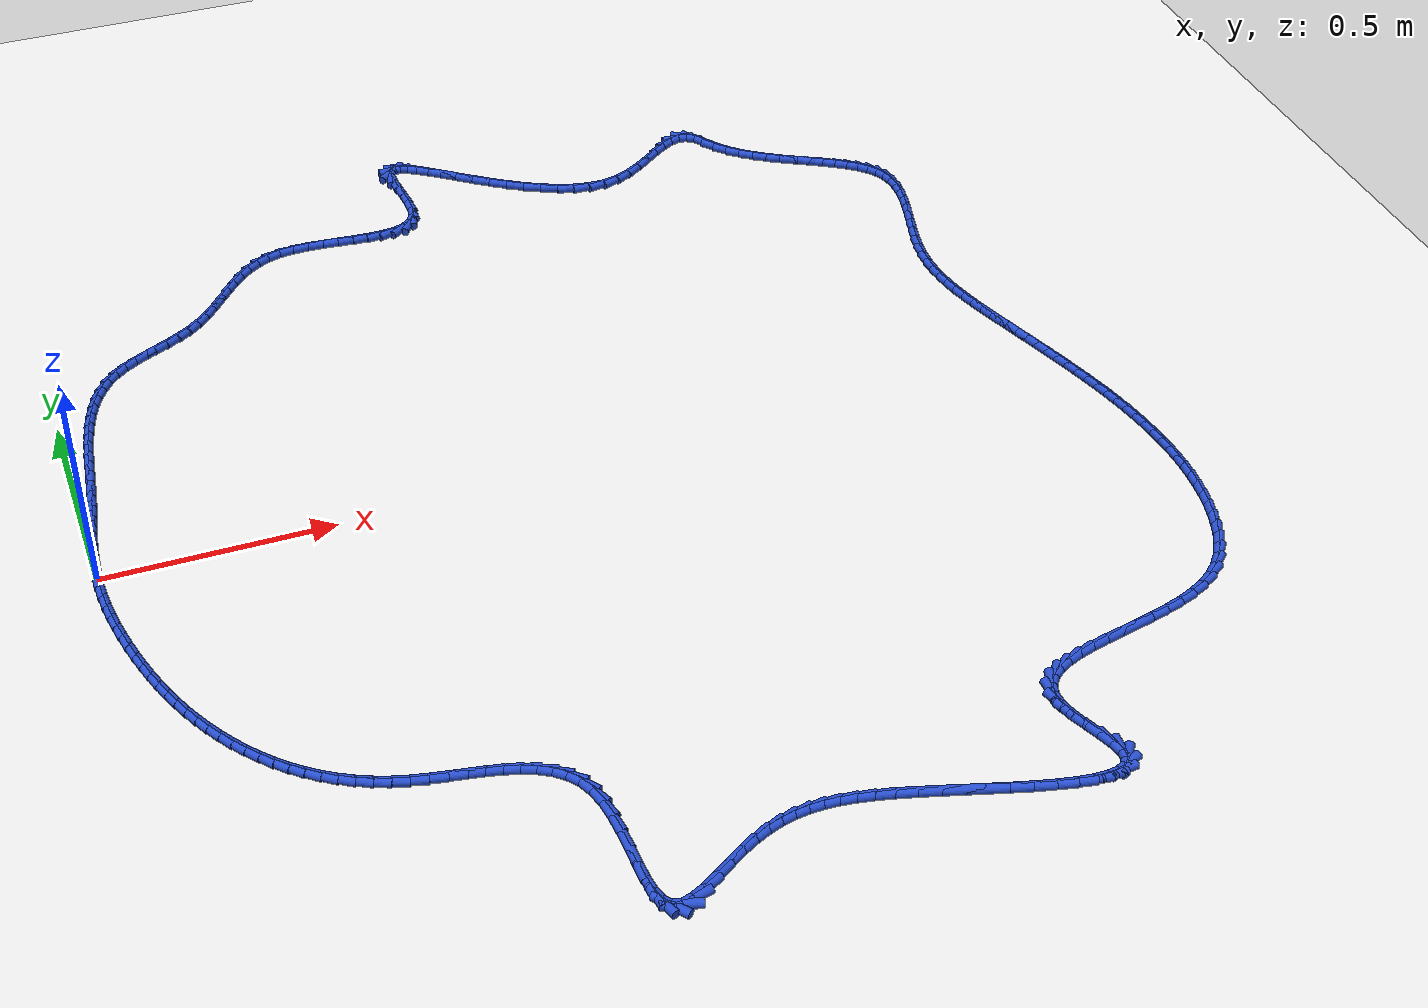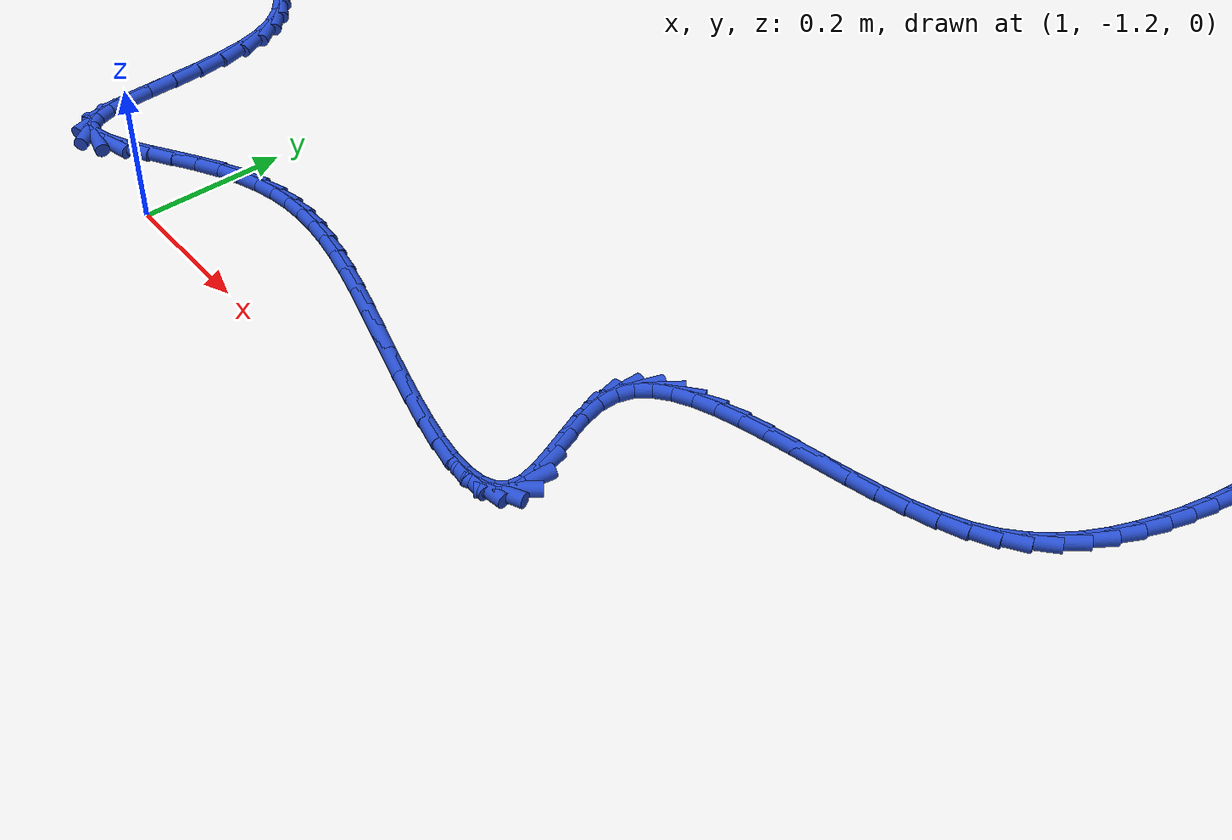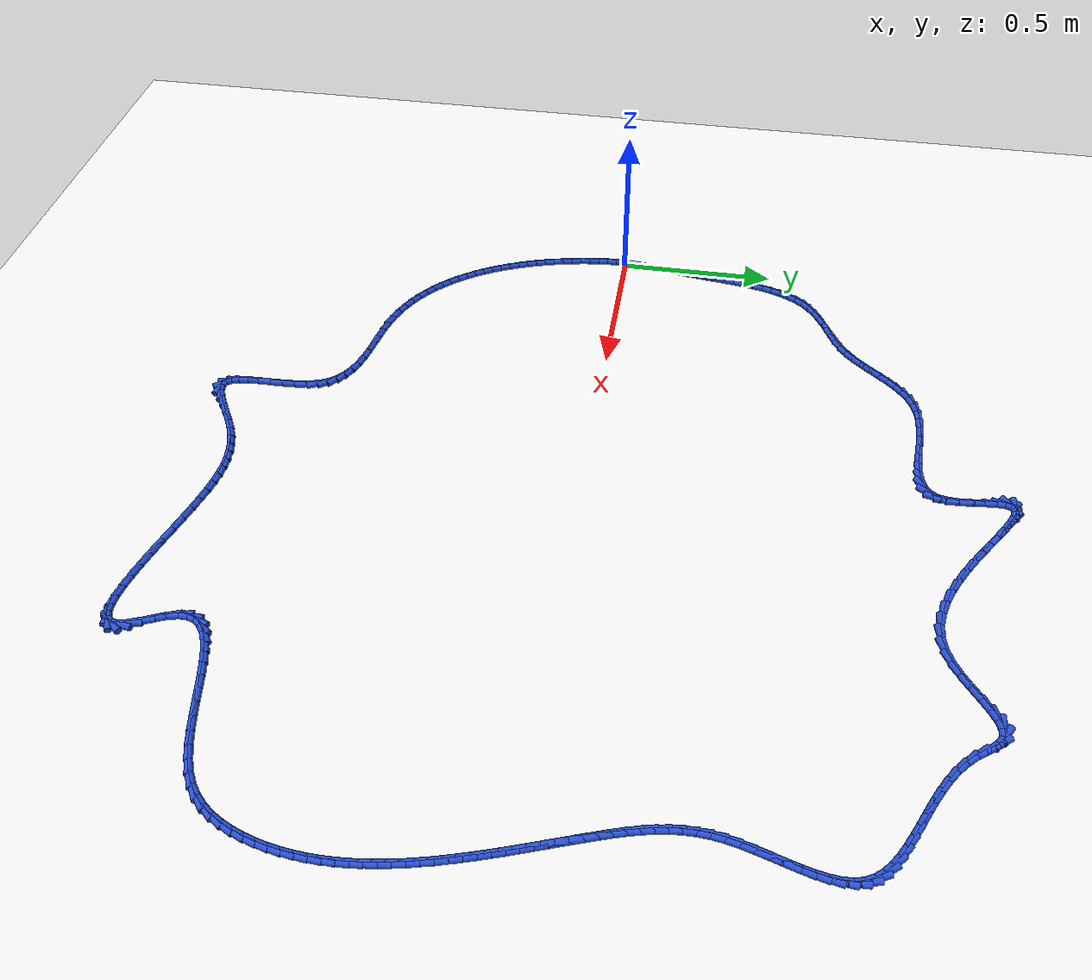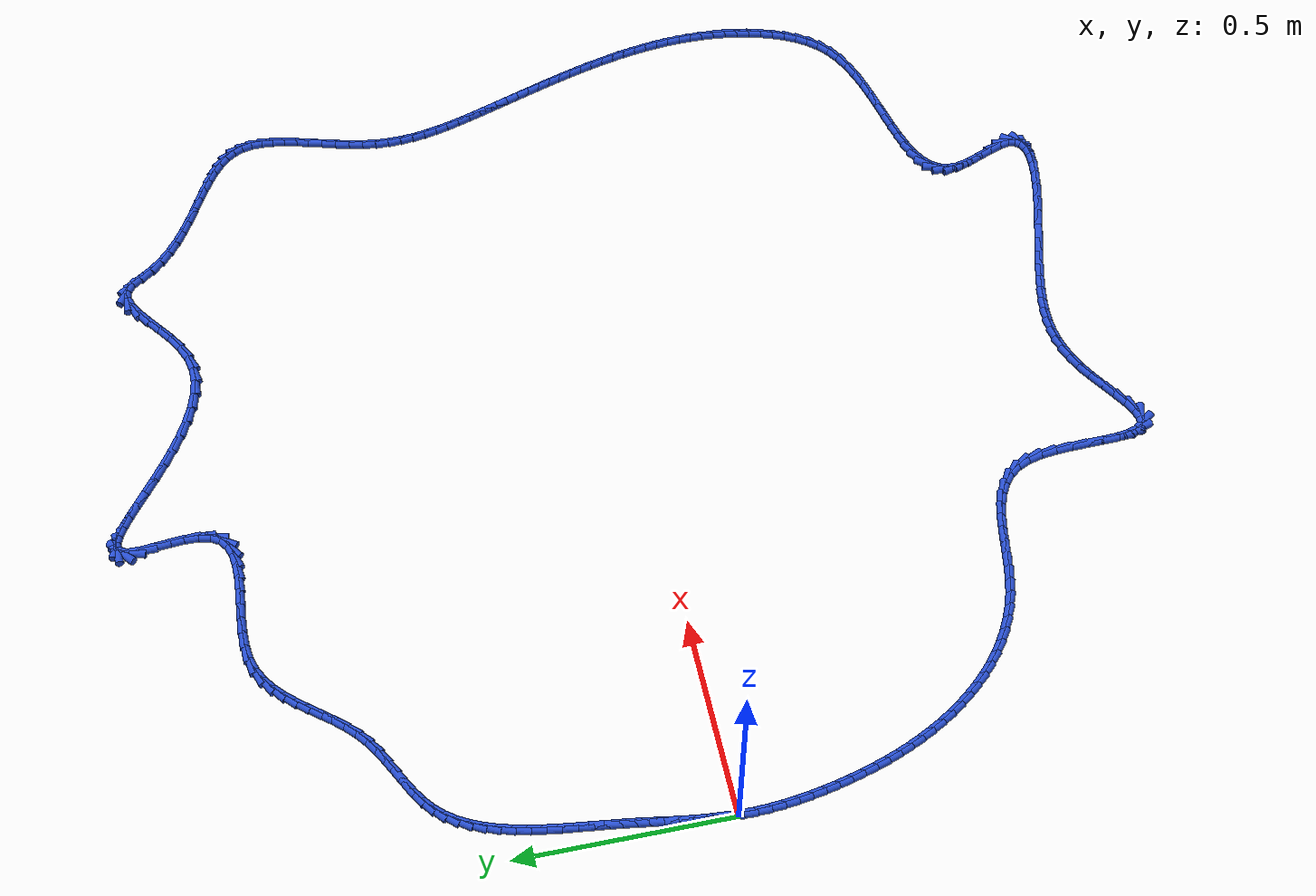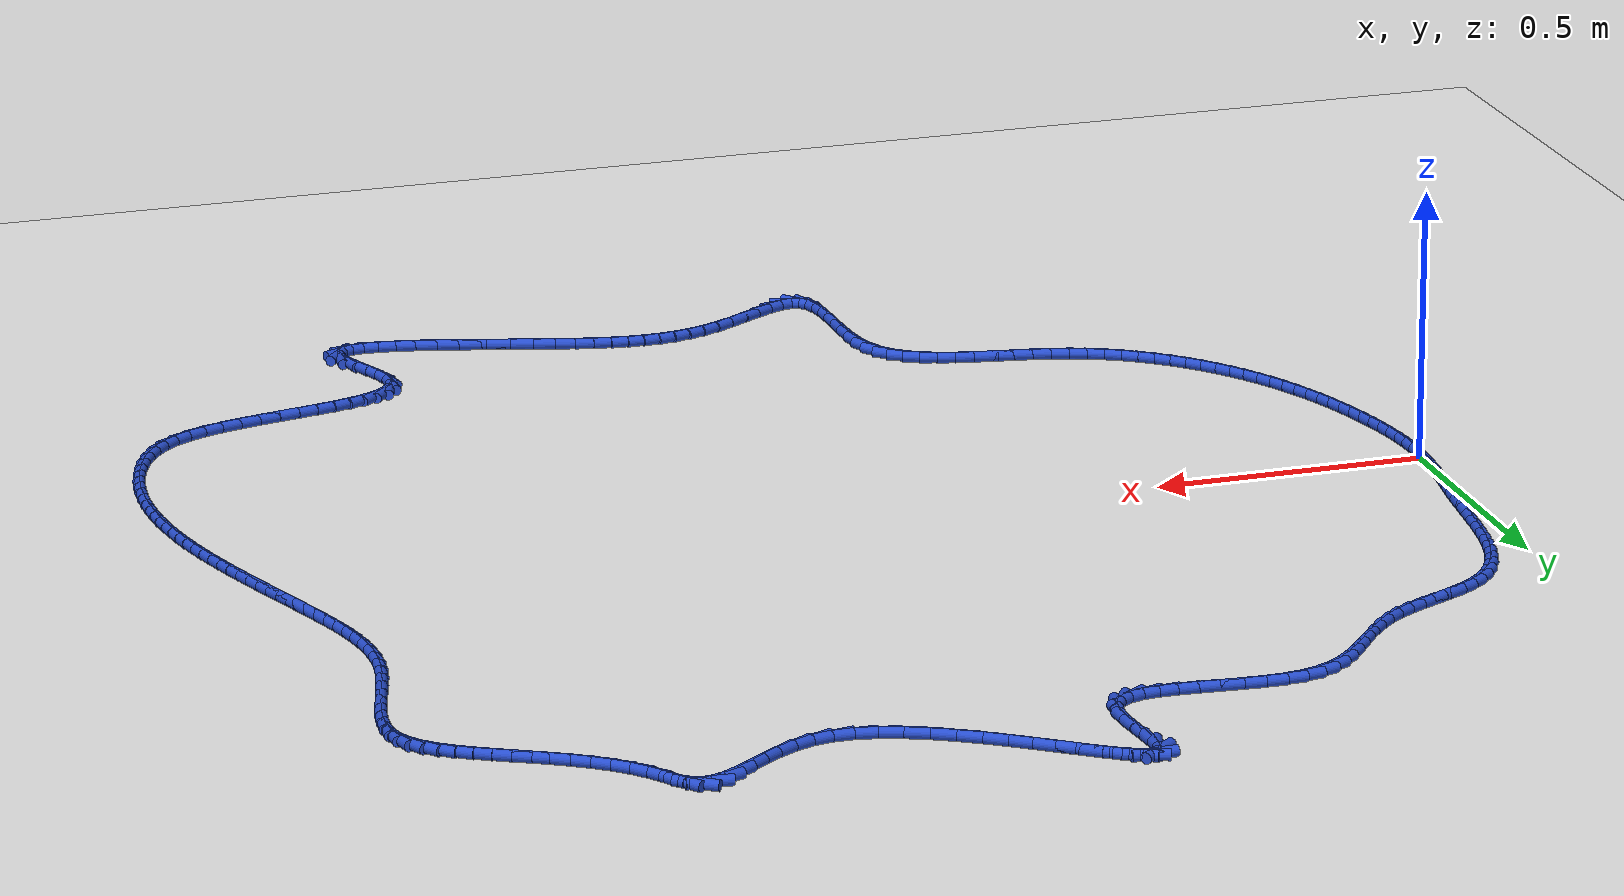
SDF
<sdf version="1.6">
 <world name="default">
  <light name="sun" type="directional">
   <pose>0 0 10 0 -0 0</pose>
   <diffuse>0.8 0.8 0.8 1</diffuse>
   <specular>0.2 0.2 0.2 1</specular>
   <attenuation>
    <range>1000</range>
    <constant>0.9</constant>
    <linear>0.01</linear>
    <quadratic>0.001</quadratic>
   </attenuation>
   <direction>-0.5 0.1 -0.9</direction>
  </light>
  <model name="ground_plane">
   <static>1</static>
   <link name="link">
    <collision name="collision">
     <geometry><plane><normal>0 0 1</normal><size>100 100</size></plane></geometry>
     <surface><friction><ode><mu>100</mu><mu2>50</mu2></ode></friction></surface>
    </collision>
    <visual name="visual">
     <cast_shadows>0</cast_shadows>
     <geometry><plane><normal>0 0 1</normal><size>100 100</size></plane></geometry>
     <material>
      <script><uri>file://media/materials/scripts/gazebo.material</uri><name>Gazebo/WhiteGlow</name></script>
     </material>
    </visual>
   </link>
  </model>
  <gravity>0 0 -9.8</gravity>
  <magnetic_field>6e-06 2.3e-05 -4.2e-05</magnetic_field>
  <atmosphere type="adiabatic"/>
  <physics name="default_physics" default="0" type="ode">
   <max_step_size>0.001</max_step_size>
   <real_time_factor>1</real_time_factor>
   <real_time_update_rate>1000</real_time_update_rate>
  </physics>
  <scene><ambient>0.4 0.4 0.4 1</ambient><background>0.7 0.7 0.7 1</background><shadows>1</shadows></scene>
  <spherical_coordinates>
   <surface_model>EARTH_WGS84</surface_model>
   <latitude_deg>0</latitude_deg>
   <longitude_deg>0</longitude_deg>
   <elevation>0</elevation>
   <heading_deg>0</heading_deg>
  </spherical_coordinates>
  <model name="line">
   <link name="link_0">
    <pose>-8.673617379884035e-19 2.7755575615628914e-17 0.01 0 1.57 1.5227078430501169</pose>
    <collision name="collision">
     <geometry><cylinder><radius>0.01</radius><length>0.08</length></cylinder></geometry>
    </collision>
    <visual name="visual">
     <material>
      <script><name>Gazebo/Blue</name><uri>file://media/materials/scripts/gazebo.material</uri></script>
     </material>
     <geometry><cylinder><radius>0.01</radius><length>0.08</length></cylinder></geometry>
    </visual>
   </link>
   <link name="link_1">
    <pose>0.0014766979700488309 0.030684259317045944 0.01 0 1.57 1.484574046072524</pose>
    <collision name="collision">
     <geometry><cylinder><radius>0.01</radius><length>0.08</length></cylinder></geometry>
    </collision>
    <visual name="visual">
     <material>
      <script><name>Gazebo/Blue</name><uri>file://media/materials/scripts/gazebo.material</uri></script>
     </material>
     <geometry><cylinder><radius>0.01</radius><length>0.08</length></cylinder></geometry>
    </visual>
   </link>
   <link name="link_2">
    <pose>0.004117510956563853 0.06123628758839806 0.01 0 1.57 1.4543443842008996</pose>
    <collision name="collision">
     <geometry><cylinder><radius>0.01</radius><length>0.08</length></cylinder></geometry>
    </collision>
    <visual name="visual">
     <material>
      <script><name>Gazebo/Blue</name><uri>file://media/materials/scripts/gazebo.material</uri></script>
     </material>
     <geometry><cylinder><radius>0.01</radius><length>0.08</length></cylinder></geometry>
    </visual>
   </link>
   <link name="link_3">
    <pose>0.007690861254964938 0.09178264685997742 0.01 0 1.57 1.4323114525035265</pose>
    <collision name="collision">
     <geometry><cylinder><radius>0.01</radius><length>0.08</length></cylinder></geometry>
    </collision>
    <visual name="visual">
     <material>
      <script><name>Gazebo/Blue</name><uri>file://media/materials/scripts/gazebo.material</uri></script>
     </material>
     <geometry><cylinder><radius>0.01</radius><length>0.08</length></cylinder></geometry>
    </visual>
   </link>
   <link name="link_4">
    <pose>0.011965171160671998 0.12244989917770505 0.01 0 1.57 1.418539389519517</pose>
    <collision name="collision">
     <geometry><cylinder><radius>0.01</radius><length>0.08</length></cylinder></geometry>
    </collision>
    <visual name="visual">
     <material>
      <script><name>Gazebo/Blue</name><uri>file://media/materials/scripts/gazebo.material</uri></script>
     </material>
     <geometry><cylinder><radius>0.01</radius><length>0.08</length></cylinder></geometry>
    </visual>
   </link>
   <link name="link_5">
    <pose>0.016708862969104895 0.1533646065875019 0.01 0 1.57 1.4129108738066924</pose>
    <collision name="collision">
     <geometry><cylinder><radius>0.01</radius><length>0.08</length></cylinder></geometry>
    </collision>
    <visual name="visual">
     <material>
      <script><name>Gazebo/Blue</name><uri>file://media/materials/scripts/gazebo.material</uri></script>
     </material>
     <geometry><cylinder><radius>0.01</radius><length>0.08</length></cylinder></geometry>
    </visual>
   </link>
   <link name="link_6">
    <pose>0.021690358975683527 0.1846533311352891 0.01 0 1.57 1.4151657299652882</pose>
    <collision name="collision">
     <geometry><cylinder><radius>0.01</radius><length>0.08</length></cylinder></geometry>
    </collision>
    <visual name="visual">
     <material>
      <script><name>Gazebo/Blue</name><uri>file://media/materials/scripts/gazebo.material</uri></script>
     </material>
     <geometry><cylinder><radius>0.01</radius><length>0.08</length></cylinder></geometry>
    </visual>
   </link>
   <link name="link_7">
    <pose>0.026678081475827765 0.21644263486698756 0.01 0 1.57 1.424927590133822</pose>
    <collision name="collision">
     <geometry><cylinder><radius>0.01</radius><length>0.08</length></cylinder></geometry>
    </collision>
    <visual name="visual">
     <material>
      <script><name>Gazebo/Blue</name><uri>file://media/materials/scripts/gazebo.material</uri></script>
     </material>
     <geometry><cylinder><radius>0.01</radius><length>0.08</length></cylinder></geometry>
    </visual>
   </link>
   <link name="link_8">
    <pose>0.0314404527764978 0.24885907981941502 0.01 0 1.57 1.4389313910487087</pose>
    <collision name="collision">
     <geometry><cylinder><radius>0.01</radius><length>0.08</length></cylinder></geometry>
    </collision>
    <visual name="visual">
     <material>
      <script><name>Gazebo/Blue</name><uri>file://media/materials/scripts/gazebo.material</uri></script>
     </material>
     <geometry><cylinder><radius>0.01</radius><length>0.08</length></cylinder></geometry>
    </visual>
   </link>
   <link name="link_9">
    <pose>0.03583105232287879 0.2819620539237671 0.01 0 1.57 1.4461551996176942</pose>
    <collision name="collision">
     <geometry><cylinder><radius>0.01</radius><length>0.08</length></cylinder></geometry>
    </collision>
    <visual name="visual">
     <material>
      <script><name>Gazebo/Blue</name><uri>file://media/materials/scripts/gazebo.material</uri></script>
     </material>
     <geometry><cylinder><radius>0.01</radius><length>0.08</length></cylinder></geometry>
    </visual>
   </link>
   <link name="link_10">
    <pose>0.04003885294282734 0.31554637832350824 0.01 0 1.57 1.4443409081162084</pose>
    <collision name="collision">
     <geometry><cylinder><radius>0.01</radius><length>0.08</length></cylinder></geometry>
    </collision>
    <visual name="visual">
     <material>
      <script><name>Gazebo/Blue</name><uri>file://media/materials/scripts/gazebo.material</uri></script>
     </material>
     <geometry><cylinder><radius>0.01</radius><length>0.08</length></cylinder></geometry>
    </visual>
   </link>
   <link name="link_11">
    <pose>0.04433538707058213 0.3493417490553315 0.01 0 1.57 1.4336270910488593</pose>
    <collision name="collision">
     <geometry><cylinder><radius>0.01</radius><length>0.08</length></cylinder></geometry>
    </collision>
    <visual name="visual">
     <material>
      <script><name>Gazebo/Blue</name><uri>file://media/materials/scripts/gazebo.material</uri></script>
     </material>
     <geometry><cylinder><radius>0.01</radius><length>0.08</length></cylinder></geometry>
    </visual>
   </link>
   <link name="link_12">
    <pose>0.04899218714038191 0.3830778621559303 0.01 0 1.57 1.4137891010803572</pose>
    <collision name="collision">
     <geometry><cylinder><radius>0.01</radius><length>0.08</length></cylinder></geometry>
    </collision>
    <visual name="visual">
     <material>
      <script><name>Gazebo/Blue</name><uri>file://media/materials/scripts/gazebo.material</uri></script>
     </material>
     <geometry><cylinder><radius>0.01</radius><length>0.08</length></cylinder></geometry>
    </visual>
   </link>
   <link name="link_13">
    <pose>0.05428078558646535 0.41648441366199773 0.01 0 1.57 1.3842508964110392</pose>
    <collision name="collision">
     <geometry><cylinder><radius>0.01</radius><length>0.08</length></cylinder></geometry>
    </collision>
    <visual name="visual">
     <material>
      <script><name>Gazebo/Blue</name><uri>file://media/materials/scripts/gazebo.material</uri></script>
     </material>
     <geometry><cylinder><radius>0.01</radius><length>0.08</length></cylinder></geometry>
    </visual>
   </link>
   <link name="link_14">
    <pose>0.06047271484307115 0.4492910996102269 0.01 0 1.57 1.3440918055485607</pose>
    <collision name="collision">
     <geometry><cylinder><radius>0.01</radius><length>0.08</length></cylinder></geometry>
    </collision>
    <visual name="visual">
     <material>
      <script><name>Gazebo/Blue</name><uri>file://media/materials/scripts/gazebo.material</uri></script>
     </material>
     <geometry><cylinder><radius>0.01</radius><length>0.08</length></cylinder></geometry>
    </visual>
   </link>
   <link name="link_15">
    <pose>0.06783950734443803 0.48122761603731096 0.01 0 1.57 1.292066856727231</pose>
    <collision name="collision">
     <geometry><cylinder><radius>0.01</radius><length>0.08</length></cylinder></geometry>
    </collision>
    <visual name="visual">
     <material>
      <script><name>Gazebo/Blue</name><uri>file://media/materials/scripts/gazebo.material</uri></script>
     </material>
     <geometry><cylinder><radius>0.01</radius><length>0.08</length></cylinder></geometry>
    </visual>
   </link>
   <link name="link_16">
    <pose>0.07665269552480472 0.5120236589799433 0.01 0 1.57 1.2266748727406762</pose>
    <collision name="collision">
     <geometry><cylinder><radius>0.01</radius><length>0.08</length></cylinder></geometry>
    </collision>
    <visual name="visual">
     <material>
      <script><name>Gazebo/Blue</name><uri>file://media/materials/scripts/gazebo.material</uri></script>
     </material>
     <geometry><cylinder><radius>0.01</radius><length>0.08</length></cylinder></geometry>
    </visual>
   </link>
   <link name="link_17">
    <pose>0.0871838118184099 0.5414089244748169 0.01 0 1.57 1.1463318288702347</pose>
    <collision name="collision">
     <geometry><cylinder><radius>0.01</radius><length>0.08</length></cylinder></geometry>
    </collision>
    <visual name="visual">
     <material>
      <script><name>Gazebo/Blue</name><uri>file://media/materials/scripts/gazebo.material</uri></script>
     </material>
     <geometry><cylinder><radius>0.01</radius><length>0.08</length></cylinder></geometry>
    </visual>
   </link>
   <link name="link_18">
    <pose>0.09970438865949227 0.569113108558625 0.01 0 1.57 1.049729572246691</pose>
    <collision name="collision">
     <geometry><cylinder><radius>0.01</radius><length>0.08</length></cylinder></geometry>
    </collision>
    <visual name="visual">
     <material>
      <script><name>Gazebo/Blue</name><uri>file://media/materials/scripts/gazebo.material</uri></script>
     </material>
     <geometry><cylinder><radius>0.01</radius><length>0.08</length></cylinder></geometry>
    </visual>
   </link>
   <link name="link_19">
    <pose>0.11448595848229048 0.5948659072680608 0.01 0 1.57 0.9364479517494522</pose>
    <collision name="collision">
     <geometry><cylinder><radius>0.01</radius><length>0.08</length></cylinder></geometry>
    </collision>
    <visual name="visual">
     <material>
      <script><name>Gazebo/Blue</name><uri>file://media/materials/scripts/gazebo.material</uri></script>
     </material>
     <geometry><cylinder><radius>0.01</radius><length>0.08</length></cylinder></geometry>
    </visual>
   </link>
   <link name="link_20">
    <pose>0.1318000537210434 0.6183970166398175 0.01 0 1.57 0.8077711082801686</pose>
    <collision name="collision">
     <geometry><cylinder><radius>0.01</radius><length>0.08</length></cylinder></geometry>
    </collision>
    <visual name="visual">
     <material>
      <script><name>Gazebo/Blue</name><uri>file://media/materials/scripts/gazebo.material</uri></script>
     </material>
     <geometry><cylinder><radius>0.01</radius><length>0.08</length></cylinder></geometry>
    </visual>
   </link>
   <link name="link_21">
    <pose>0.15191820680998963 0.6394361327105883 0.01 0 1.57 0.6718495499952478</pose>
    <collision name="collision">
     <geometry><cylinder><radius>0.01</radius><length>0.08</length></cylinder></geometry>
    </collision>
    <visual name="visual">
     <material>
      <script><name>Gazebo/Blue</name><uri>file://media/materials/scripts/gazebo.material</uri></script>
     </material>
     <geometry><cylinder><radius>0.01</radius><length>0.08</length></cylinder></geometry>
    </visual>
   </link>
   <link name="link_22">
    <pose>0.1750202774864406 0.6578084944364359 0.01 0 1.57 0.5637679732753983</pose>
    <collision name="collision">
     <geometry><cylinder><radius>0.01</radius><length>0.08</length></cylinder></geometry>
    </collision>
    <visual name="visual">
     <material>
      <script><name>Gazebo/Blue</name><uri>file://media/materials/scripts/gazebo.material</uri></script>
     </material>
     <geometry><cylinder><radius>0.01</radius><length>0.08</length></cylinder></geometry>
    </visual>
   </link>
   <link name="link_23">
    <pose>0.2006442873387206 0.6740082759370251 0.01 0 1.57 0.4953028696086822</pose>
    <collision name="collision">
     <geometry><cylinder><radius>0.01</radius><length>0.08</length></cylinder></geometry>
    </collision>
    <visual name="visual">
     <material>
      <script><name>Gazebo/Blue</name><uri>file://media/materials/scripts/gazebo.material</uri></script>
     </material>
     <geometry><cylinder><radius>0.01</radius><length>0.08</length></cylinder></geometry>
    </visual>
   </link>
   <link name="link_24">
    <pose>0.22805397603519736 0.6888155128397677 0.01 0 1.57 0.4627128845364818</pose>
    <collision name="collision">
     <geometry><cylinder><radius>0.01</radius><length>0.08</length></cylinder></geometry>
    </collision>
    <visual name="visual">
     <material>
      <script><name>Gazebo/Blue</name><uri>file://media/materials/scripts/gazebo.material</uri></script>
     </material>
     <geometry><cylinder><radius>0.01</radius><length>0.08</length></cylinder></geometry>
    </visual>
   </link>
   <link name="link_25">
    <pose>0.25651205185897796 0.7030113157001865 0.01 0 1.57 0.46311617016512074</pose>
    <collision name="collision">
     <geometry><cylinder><radius>0.01</radius><length>0.08</length></cylinder></geometry>
    </collision>
    <visual name="visual">
     <material>
      <script><name>Gazebo/Blue</name><uri>file://media/materials/scripts/gazebo.material</uri></script>
     </material>
     <geometry><cylinder><radius>0.01</radius><length>0.08</length></cylinder></geometry>
    </visual>
   </link>
   <link name="link_26">
    <pose>0.2852812230931695 0.717376795073803 0.01 0 1.57 0.4954353351867064</pose>
    <collision name="collision">
     <geometry><cylinder><radius>0.01</radius><length>0.08</length></cylinder></geometry>
    </collision>
    <visual name="visual">
     <material>
      <script><name>Gazebo/Blue</name><uri>file://media/materials/scripts/gazebo.material</uri></script>
     </material>
     <geometry><cylinder><radius>0.01</radius><length>0.08</length></cylinder></geometry>
    </visual>
   </link>
   <link name="link_27">
    <pose>0.3136241980208788 0.7326930615161387 0.01 0 1.57 0.5602111921854945</pose>
    <collision name="collision">
     <geometry><cylinder><radius>0.01</radius><length>0.08</length></cylinder></geometry>
    </collision>
    <visual name="visual">
     <material>
      <script><name>Gazebo/Blue</name><uri>file://media/materials/scripts/gazebo.material</uri></script>
     </material>
     <geometry><cylinder><radius>0.01</radius><length>0.08</length></cylinder></geometry>
    </visual>
   </link>
   <link name="link_28">
    <pose>0.3408036849252134 0.7497412255827155 0.01 0 1.57 0.657716649335117</pose>
    <collision name="collision">
     <geometry><cylinder><radius>0.01</radius><length>0.08</length></cylinder></geometry>
    </collision>
    <visual name="visual">
     <material>
      <script><name>Gazebo/Blue</name><uri>file://media/materials/scripts/gazebo.material</uri></script>
     </material>
     <geometry><cylinder><radius>0.01</radius><length>0.08</length></cylinder></geometry>
    </visual>
   </link>
   <link name="link_29">
    <pose>0.36609989519673886 0.7692813509312098 0.01 0 1.57 0.7597730746519437</pose>
    <collision name="collision">
     <geometry><cylinder><radius>0.01</radius><length>0.08</length></cylinder></geometry>
    </collision>
    <visual name="visual">
     <material>
      <script><name>Gazebo/Blue</name><uri>file://media/materials/scripts/gazebo.material</uri></script>
     </material>
     <geometry><cylinder><radius>0.01</radius><length>0.08</length></cylinder></geometry>
    </visual>
   </link>
   <link name="link_30">
    <pose>0.38936596705056237 0.7913845759883146 0.01 0 1.57 0.8320810749532079</pose>
    <collision name="collision">
     <geometry><cylinder><radius>0.01</radius><length>0.08</length></cylinder></geometry>
    </collision>
    <visual name="visual">
     <material>
      <script><name>Gazebo/Blue</name><uri>file://media/materials/scripts/gazebo.material</uri></script>
     </material>
     <geometry><cylinder><radius>0.01</radius><length>0.08</length></cylinder></geometry>
    </visual>
   </link>
   <link name="link_31">
    <pose>0.4111424599092808 0.815295438306289 0.01 0 1.57 0.8735451435835182</pose>
    <collision name="collision">
     <geometry><cylinder><radius>0.01</radius><length>0.08</length></cylinder></geometry>
    </collision>
    <visual name="visual">
     <material>
      <script><name>Gazebo/Blue</name><uri>file://media/materials/scripts/gazebo.material</uri></script>
     </material>
     <geometry><cylinder><radius>0.01</radius><length>0.08</length></cylinder></geometry>
    </visual>
   </link>
   <link name="link_32">
    <pose>0.43201057371116647 0.8402096065845998 0.01 0 1.57 0.8852142958517611</pose>
    <collision name="collision">
     <geometry><cylinder><radius>0.01</radius><length>0.08</length></cylinder></geometry>
    </collision>
    <visual name="visual">
     <material>
      <script><name>Gazebo/Blue</name><uri>file://media/materials/scripts/gazebo.material</uri></script>
     </material>
     <geometry><cylinder><radius>0.01</radius><length>0.08</length></cylinder></geometry>
    </visual>
   </link>
   <link name="link_33">
    <pose>0.4525515083944917 0.865322749522714 0.01 0 1.57 0.8671713900985939</pose>
    <collision name="collision">
     <geometry><cylinder><radius>0.01</radius><length>0.08</length></cylinder></geometry>
    </collision>
    <visual name="visual">
     <material>
      <script><name>Gazebo/Blue</name><uri>file://media/materials/scripts/gazebo.material</uri></script>
     </material>
     <geometry><cylinder><radius>0.01</radius><length>0.08</length></cylinder></geometry>
    </visual>
   </link>
   <link name="link_34">
    <pose>0.473346463897529 0.8898305358200981 0.01 0 1.57 0.8182050496985457</pose>
    <collision name="collision">
     <geometry><cylinder><radius>0.01</radius><length>0.08</length></cylinder></geometry>
    </collision>
    <visual name="visual">
     <material>
      <script><name>Gazebo/Blue</name><uri>file://media/materials/scripts/gazebo.material</uri></script>
     </material>
     <geometry><cylinder><radius>0.01</radius><length>0.08</length></cylinder></geometry>
    </visual>
   </link>
   <link name="link_35">
    <pose>0.4949766401585505 0.9129286341762192 0.01 0 1.57 0.7362121763774888</pose>
    <collision name="collision">
     <geometry><cylinder><radius>0.01</radius><length>0.08</length></cylinder></geometry>
    </collision>
    <visual name="visual">
     <material>
      <script><name>Gazebo/Blue</name><uri>file://media/materials/scripts/gazebo.material</uri></script>
     </material>
     <geometry><cylinder><radius>0.01</radius><length>0.08</length></cylinder></geometry>
    </visual>
   </link>
   <link name="link_36">
    <pose>0.5180232371158289 0.9338127132905439 0.01 0 1.57 0.6196411537167645</pose>
    <collision name="collision">
     <geometry><cylinder><radius>0.01</radius><length>0.08</length></cylinder></geometry>
    </collision>
    <visual name="visual">
     <material>
      <script><name>Gazebo/Blue</name><uri>file://media/materials/scripts/gazebo.material</uri></script>
     </material>
     <geometry><cylinder><radius>0.01</radius><length>0.08</length></cylinder></geometry>
    </visual>
   </link>
   <link name="link_37">
    <pose>0.5430674547076363 0.9516784418625395 0.01 0 1.57 0.47033045299978116</pose>
    <collision name="collision">
     <geometry><cylinder><radius>0.01</radius><length>0.08</length></cylinder></geometry>
    </collision>
    <visual name="visual">
     <material>
      <script><name>Gazebo/Blue</name><uri>file://media/materials/scripts/gazebo.material</uri></script>
     </material>
     <geometry><cylinder><radius>0.01</radius><length>0.08</length></cylinder></geometry>
    </visual>
   </link>
   <link name="link_38">
    <pose>0.5706904928722454 0.9657214885916727 0.01 0 1.57 0.29703490595790244</pose>
    <collision name="collision">
     <geometry><cylinder><radius>0.01</radius><length>0.08</length></cylinder></geometry>
    </collision>
    <visual name="visual">
     <material>
      <script><name>Gazebo/Blue</name><uri>file://media/materials/scripts/gazebo.material</uri></script>
     </material>
     <geometry><cylinder><radius>0.01</radius><length>0.08</length></cylinder></geometry>
    </visual>
   </link>
   <link name="link_39">
    <pose>0.601469520867363 0.975142653476272 0.01 0 1.57 0.13520720424564975</pose>
    <collision name="collision">
     <geometry><cylinder><radius>0.01</radius><length>0.08</length></cylinder></geometry>
    </collision>
    <visual name="visual">
     <material>
      <script><name>Gazebo/Blue</name><uri>file://media/materials/scripts/gazebo.material</uri></script>
     </material>
     <geometry><cylinder><radius>0.01</radius><length>0.08</length></cylinder></geometry>
    </visual>
   </link>
   <link name="link_40">
    <pose>0.6354885854531444 0.9797705111223965 0.01 0 1.57 0.02434971431885352</pose>
    <collision name="collision">
     <geometry><cylinder><radius>0.01</radius><length>0.08</length></cylinder></geometry>
    </collision>
    <visual name="visual">
     <material>
      <script><name>Gazebo/Blue</name><uri>file://media/materials/scripts/gazebo.material</uri></script>
     </material>
     <geometry><cylinder><radius>0.01</radius><length>0.08</length></cylinder></geometry>
    </visual>
   </link>
   <link name="link_41">
    <pose>0.6718710924087676 0.9806565899011311 0.01 0 1.57 -0.04401826574720289</pose>
    <collision name="collision">
     <geometry><cylinder><radius>0.01</radius><length>0.08</length></cylinder></geometry>
    </collision>
    <visual name="visual">
     <material>
      <script><name>Gazebo/Blue</name><uri>file://media/materials/scripts/gazebo.material</uri></script>
     </material>
     <geometry><cylinder><radius>0.01</radius><length>0.08</length></cylinder></geometry>
    </visual>
   </link>
   <link name="link_42">
    <pose>0.7096296668553287 0.9789934486263355 0.01 0 1.57 -0.07899696149360466</pose>
    <collision name="collision">
     <geometry><cylinder><radius>0.01</radius><length>0.08</length></cylinder></geometry>
    </collision>
    <visual name="visual">
     <material>
      <script><name>Gazebo/Blue</name><uri>file://media/materials/scripts/gazebo.material</uri></script>
     </material>
     <geometry><cylinder><radius>0.01</radius><length>0.08</length></cylinder></geometry>
    </visual>
   </link>
   <link name="link_43">
    <pose>0.7477769339139229 0.9759736461118699 0.01 0 1.57 -0.08459191944908716</pose>
    <collision name="collision">
     <geometry><cylinder><radius>0.01</radius><length>0.08</length></cylinder></geometry>
    </collision>
    <visual name="visual">
     <material>
      <script><name>Gazebo/Blue</name><uri>file://media/materials/scripts/gazebo.material</uri></script>
     </material>
     <geometry><cylinder><radius>0.01</radius><length>0.08</length></cylinder></geometry>
    </visual>
   </link>
   <link name="link_44">
    <pose>0.7853255187056453 0.9727897411715933 0.01 0 1.57 -0.05986434275814405</pose>
    <collision name="collision">
     <geometry><cylinder><radius>0.01</radius><length>0.08</length></cylinder></geometry>
    </collision>
    <visual name="visual">
     <material>
      <script><name>Gazebo/Blue</name><uri>file://media/materials/scripts/gazebo.material</uri></script>
     </material>
     <geometry><cylinder><radius>0.01</radius><length>0.08</length></cylinder></geometry>
    </visual>
   </link>
   <link name="link_45">
    <pose>0.8212880463515925 0.9706342926193664 0.01 0 1.57 0.0019637119299977797</pose>
    <collision name="collision">
     <geometry><cylinder><radius>0.01</radius><length>0.08</length></cylinder></geometry>
    </collision>
    <visual name="visual">
     <material>
      <script><name>Gazebo/Blue</name><uri>file://media/materials/scripts/gazebo.material</uri></script>
     </material>
     <geometry><cylinder><radius>0.01</radius><length>0.08</length></cylinder></geometry>
    </visual>
   </link>
   <link name="link_46">
    <pose>0.8546771419728592 0.9706998592690483 0.01 0 1.57 0.11611429518518097</pose>
    <collision name="collision">
     <geometry><cylinder><radius>0.01</radius><length>0.08</length></cylinder></geometry>
    </collision>
    <visual name="visual">
     <material>
      <script><name>Gazebo/Blue</name><uri>file://media/materials/scripts/gazebo.material</uri></script>
     </material>
     <geometry><cylinder><radius>0.01</radius><length>0.08</length></cylinder></geometry>
    </visual>
   </link>
   <link name="link_47">
    <pose>0.8845054306905412 0.9741789999344992 0.01 0 1.57 0.30954646331296826</pose>
    <collision name="collision">
     <geometry><cylinder><radius>0.01</radius><length>0.08</length></cylinder></geometry>
    </collision>
    <visual name="visual">
     <material>
      <script><name>Gazebo/Blue</name><uri>file://media/materials/scripts/gazebo.material</uri></script>
     </material>
     <geometry><cylinder><radius>0.01</radius><length>0.08</length></cylinder></geometry>
    </visual>
   </link>
   <link name="link_48">
    <pose>0.909785537625734 0.9822642734295786 0.01 0 1.57 0.6128567439275524</pose>
    <collision name="collision">
     <geometry><cylinder><radius>0.01</radius><length>0.08</length></cylinder></geometry>
    </collision>
    <visual name="visual">
     <material>
      <script><name>Gazebo/Blue</name><uri>file://media/materials/scripts/gazebo.material</uri></script>
     </material>
     <geometry><cylinder><radius>0.01</radius><length>0.08</length></cylinder></geometry>
    </visual>
   </link>
   <link name="link_49">
    <pose>0.9295300878995331 0.9961482385681466 0.01 0 1.57 1.0062030785484826</pose>
    <collision name="collision">
     <geometry><cylinder><radius>0.01</radius><length>0.08</length></cylinder></geometry>
    </collision>
    <visual name="visual">
     <material>
      <script><name>Gazebo/Blue</name><uri>file://media/materials/scripts/gazebo.material</uri></script>
     </material>
     <geometry><cylinder><radius>0.01</radius><length>0.08</length></cylinder></geometry>
    </visual>
   </link>
   <link name="link_50">
    <pose>0.9427517330875418 1.017023418780935 0.01 0 1.57 1.3525167556564872</pose>
    <collision name="collision">
     <geometry><cylinder><radius>0.01</radius><length>0.08</length></cylinder></geometry>
    </collision>
    <visual name="visual">
     <material>
      <script><name>Gazebo/Blue</name><uri>file://media/materials/scripts/gazebo.material</uri></script>
     </material>
     <geometry><cylinder><radius>0.01</radius><length>0.08</length></cylinder></geometry>
    </visual>
   </link>
   <link name="link_51">
    <pose>0.9490293975666655 1.0453249428465847 0.01 0 1.57 1.542768420031275</pose>
    <collision name="collision">
     <geometry><cylinder><radius>0.01</radius><length>0.08</length></cylinder></geometry>
    </collision>
    <visual name="visual">
     <material>
      <script><name>Gazebo/Blue</name><uri>file://media/materials/scripts/gazebo.material</uri></script>
     </material>
     <geometry><cylinder><radius>0.01</radius><length>0.08</length></cylinder></geometry>
    </visual>
   </link>
   <link name="link_52">
    <pose>0.9499672931821174 1.0787791004578342 0.01 0 1.57 -1.5052532845175577</pose>
    <collision name="collision">
     <geometry><cylinder><radius>0.01</radius><length>0.08</length></cylinder></geometry>
    </collision>
    <visual name="visual">
     <material>
      <script><name>Gazebo/Blue</name><uri>file://media/materials/scripts/gazebo.material</uri></script>
     </material>
     <geometry><cylinder><radius>0.01</radius><length>0.08</length></cylinder></geometry>
    </visual>
   </link>
   <link name="link_53">
    <pose>0.9476222302854045 1.1145068269845204 0.01 0 1.57 -1.4694650756756558</pose>
    <collision name="collision">
     <geometry><cylinder><radius>0.01</radius><length>0.08</length></cylinder></geometry>
    </collision>
    <visual name="visual">
     <material>
      <script><name>Gazebo/Blue</name><uri>file://media/materials/scripts/gazebo.material</uri></script>
     </material>
     <geometry><cylinder><radius>0.01</radius><length>0.08</length></cylinder></geometry>
    </visual>
   </link>
   <link name="link_54">
    <pose>0.9440510192280328 1.1496290577964803 0.01 0 1.57 -1.4843890497253098</pose>
    <collision name="collision">
     <geometry><cylinder><radius>0.01</radius><length>0.08</length></cylinder></geometry>
    </collision>
    <visual name="visual">
     <material>
      <script><name>Gazebo/Blue</name><uri>file://media/materials/scripts/gazebo.material</uri></script>
     </material>
     <geometry><cylinder><radius>0.01</radius><length>0.08</length></cylinder></geometry>
    </visual>
   </link>
   <link name="link_55">
    <pose>0.9413104703615077 1.1812667282635492 0.01 0 1.57 1.5649831687516584</pose>
    <collision name="collision">
     <geometry><cylinder><radius>0.01</radius><length>0.08</length></cylinder></geometry>
    </collision>
    <visual name="visual">
     <material>
      <script><name>Gazebo/Blue</name><uri>file://media/materials/scripts/gazebo.material</uri></script>
     </material>
     <geometry><cylinder><radius>0.01</radius><length>0.08</length></cylinder></geometry>
    </visual>
   </link>
   <link name="link_56">
    <pose>0.9414573940373363 1.206540773755564 0.01 0 1.57 1.2874305760909794</pose>
    <collision name="collision">
     <geometry><cylinder><radius>0.01</radius><length>0.08</length></cylinder></geometry>
    </collision>
    <visual name="visual">
     <material>
      <script><name>Gazebo/Blue</name><uri>file://media/materials/scripts/gazebo.material</uri></script>
     </material>
     <geometry><cylinder><radius>0.01</radius><length>0.08</length></cylinder></geometry>
    </visual>
   </link>
   <link name="link_57">
    <pose>0.9462603256378946 1.223034248461938 0.01 0 1.57 0.6835445726071061</pose>
    <collision name="collision">
     <geometry><cylinder><radius>0.01</radius><length>0.08</length></cylinder></geometry>
    </collision>
    <visual name="visual">
     <material>
      <script><name>Gazebo/Blue</name><uri>file://media/materials/scripts/gazebo.material</uri></script>
     </material>
     <geometry><cylinder><radius>0.01</radius><length>0.08</length></cylinder></geometry>
    </visual>
   </link>
   <link name="link_58">
    <pose>0.9558956039949503 1.2308825752106973 0.01 0 1.57 0.015247276026641877</pose>
    <collision name="collision">
     <geometry><cylinder><radius>0.01</radius><length>0.08</length></cylinder></geometry>
    </collision>
    <visual name="visual">
     <material>
      <script><name>Gazebo/Blue</name><uri>file://media/materials/scripts/gazebo.material</uri></script>
     </material>
     <geometry><cylinder><radius>0.01</radius><length>0.08</length></cylinder></geometry>
    </visual>
   </link>
   <link name="link_59">
    <pose>0.9699928845133576 1.2310975369963089 0.01 0 1.57 -0.3386264770691686</pose>
    <collision name="collision">
     <geometry><cylinder><radius>0.01</radius><length>0.08</length></cylinder></geometry>
    </collision>
    <visual name="visual">
     <material>
      <script><name>Gazebo/Blue</name><uri>file://media/materials/scripts/gazebo.material</uri></script>
     </material>
     <geometry><cylinder><radius>0.01</radius><length>0.08</length></cylinder></geometry>
    </visual>
   </link>
   <link name="link_60">
    <pose>0.9881813290093746 1.2246917080598054 0.01 0 1.57 -0.501588560847529</pose>
    <collision name="collision">
     <geometry><cylinder><radius>0.01</radius><length>0.08</length></cylinder></geometry>
    </collision>
    <visual name="visual">
     <material>
      <script><name>Gazebo/Blue</name><uri>file://media/materials/scripts/gazebo.material</uri></script>
     </material>
     <geometry><cylinder><radius>0.01</radius><length>0.08</length></cylinder></geometry>
    </visual>
   </link>
   <link name="link_61">
    <pose>1.0100900992992603 1.2126776626422224 0.01 0 1.57 -0.5816954419464128</pose>
    <collision name="collision">
     <geometry><cylinder><radius>0.01</radius><length>0.08</length></cylinder></geometry>
    </collision>
    <visual name="visual">
     <material>
      <script><name>Gazebo/Blue</name><uri>file://media/materials/scripts/gazebo.material</uri></script>
     </material>
     <geometry><cylinder><radius>0.01</radius><length>0.08</length></cylinder></geometry>
    </visual>
   </link>
   <link name="link_62">
    <pose>1.0353483571992719 1.1960679749845928 0.01 0 1.57 -0.6208011964271664</pose>
    <collision name="collision">
     <geometry><cylinder><radius>0.01</radius><length>0.08</length></cylinder></geometry>
    </collision>
    <visual name="visual">
     <material>
      <script><name>Gazebo/Blue</name><uri>file://media/materials/scripts/gazebo.material</uri></script>
     </material>
     <geometry><cylinder><radius>0.01</radius><length>0.08</length></cylinder></geometry>
    </visual>
   </link>
   <link name="link_63">
    <pose>1.063585264525669 1.1758752193279505 0.01 0 1.57 -0.6357735603474983</pose>
    <collision name="collision">
     <geometry><cylinder><radius>0.01</radius><length>0.08</length></cylinder></geometry>
    </collision>
    <visual name="visual">
     <material>
      <script><name>Gazebo/Blue</name><uri>file://media/materials/scripts/gazebo.material</uri></script>
     </material>
     <geometry><cylinder><radius>0.01</radius><length>0.08</length></cylinder></geometry>
    </visual>
   </link>
   <link name="link_64">
    <pose>1.0944299830947086 1.1531119699133285 0.01 0 1.57 -0.6339519979710913</pose>
    <collision name="collision">
     <geometry><cylinder><radius>0.01</radius><length>0.08</length></cylinder></geometry>
    </collision>
    <visual name="visual">
     <material>
      <script><name>Gazebo/Blue</name><uri>file://media/materials/scripts/gazebo.material</uri></script>
     </material>
     <geometry><cylinder><radius>0.01</radius><length>0.08</length></cylinder></geometry>
    </visual>
   </link>
   <link name="link_65">
    <pose>1.1275116747226495 1.1287908009817615 0.01 0 1.57 -0.6184240336682811</pose>
    <collision name="collision">
     <geometry><cylinder><radius>0.01</radius><length>0.08</length></cylinder></geometry>
    </collision>
    <visual name="visual">
     <material>
      <script><name>Gazebo/Blue</name><uri>file://media/materials/scripts/gazebo.material</uri></script>
     </material>
     <geometry><cylinder><radius>0.01</radius><length>0.08</length></cylinder></geometry>
    </visual>
   </link>
   <link name="link_66">
    <pose>1.1624595012257506 1.1039242867742827 0.01 0 1.57 -0.5899732162965794</pose>
    <collision name="collision">
     <geometry><cylinder><radius>0.01</radius><length>0.08</length></cylinder></geometry>
    </collision>
    <visual name="visual">
     <material>
      <script><name>Gazebo/Blue</name><uri>file://media/materials/scripts/gazebo.material</uri></script>
     </material>
     <geometry><cylinder><radius>0.01</radius><length>0.08</length></cylinder></geometry>
    </visual>
   </link>
   <link name="link_67">
    <pose>1.198902624420269 1.0795250015319262 0.01 0 1.57 -0.5478032008119791</pose>
    <collision name="collision">
     <geometry><cylinder><radius>0.01</radius><length>0.08</length></cylinder></geometry>
    </collision>
    <visual name="visual">
     <material>
      <script><name>Gazebo/Blue</name><uri>file://media/materials/scripts/gazebo.material</uri></script>
     </material>
     <geometry><cylinder><radius>0.01</radius><length>0.08</length></cylinder></geometry>
    </visual>
   </link>
   <link name="link_68">
    <pose>1.236470206122464 1.0566055194957253 0.01 0 1.57 -0.48973646514505537</pose>
    <collision name="collision">
     <geometry><cylinder><radius>0.01</radius><length>0.08</length></cylinder></geometry>
    </collision>
    <visual name="visual">
     <material>
      <script><name>Gazebo/Blue</name><uri>file://media/materials/scripts/gazebo.material</uri></script>
     </material>
     <geometry><cylinder><radius>0.01</radius><length>0.08</length></cylinder></geometry>
    </visual>
   </link>
   <link name="link_69">
    <pose>1.2747914081485934 1.0361784149067137 0.01 0 1.57 -0.4121753347457541</pose>
    <collision name="collision">
     <geometry><cylinder><radius>0.01</radius><length>0.08</length></cylinder></geometry>
    </collision>
    <visual name="visual">
     <material>
      <script><name>Gazebo/Blue</name><uri>file://media/materials/scripts/gazebo.material</uri></script>
     </material>
     <geometry><cylinder><radius>0.01</radius><length>0.08</length></cylinder></geometry>
    </visual>
   </link>
   <link name="link_70">
    <pose>1.3134953923149153 1.0192562620059256 0.01 0 1.57 -0.3100667684347979</pose>
    <collision name="collision">
     <geometry><cylinder><radius>0.01</radius><length>0.08</length></cylinder></geometry>
    </collision>
    <visual name="visual">
     <material>
      <script><name>Gazebo/Blue</name><uri>file://media/materials/scripts/gazebo.material</uri></script>
     </material>
     <geometry><cylinder><radius>0.01</radius><length>0.08</length></cylinder></geometry>
    </visual>
   </link>
   <link name="link_71">
    <pose>1.352211320437688 1.0068516350343941 0.01 0 1.57 -0.17734184065778916</pose>
    <collision name="collision">
     <geometry><cylinder><radius>0.01</radius><length>0.08</length></cylinder></geometry>
    </collision>
    <visual name="visual">
     <material>
      <script><name>Gazebo/Blue</name><uri>file://media/materials/scripts/gazebo.material</uri></script>
     </material>
     <geometry><cylinder><radius>0.01</radius><length>0.08</length></cylinder></geometry>
    </visual>
   </link>
   <link name="link_72">
    <pose>1.3905683543331704 0.9999771082331536 0.01 0 1.57 -0.008819228939796616</pose>
    <collision name="collision">
     <geometry><cylinder><radius>0.01</radius><length>0.08</length></cylinder></geometry>
    </collision>
    <visual name="visual">
     <material>
      <script><name>Gazebo/Blue</name><uri>file://media/materials/scripts/gazebo.material</uri></script>
     </material>
     <geometry><cylinder><radius>0.01</radius><length>0.08</length></cylinder></geometry>
    </visual>
   </link>
   <link name="link_73">
    <pose>1.4281956558176199 0.9996452558432374 0.01 0 1.57 0.19493076184710992</pose>
    <collision name="collision">
     <geometry><cylinder><radius>0.01</radius><length>0.08</length></cylinder></geometry>
    </collision>
    <visual name="visual">
     <material>
      <script><name>Gazebo/Blue</name><uri>file://media/materials/scripts/gazebo.material</uri></script>
     </material>
     <geometry><cylinder><radius>0.01</radius><length>0.08</length></cylinder></geometry>
    </visual>
   </link>
   <link name="link_74">
    <pose>1.464723219996872 1.0068571802349615 0.01 0 1.57 0.39399973062562726</pose>
    <collision name="collision">
     <geometry><cylinder><radius>0.01</radius><length>0.08</length></cylinder></geometry>
    </collision>
    <visual name="visual">
     <material>
      <script><name>Gazebo/Blue</name><uri>file://media/materials/scripts/gazebo.material</uri></script>
     </material>
     <geometry><cylinder><radius>0.01</radius><length>0.08</length></cylinder></geometry>
    </visual>
   </link>
   <link name="link_75">
    <pose>1.4998643778442444 1.0214667015796945 0.01 0 1.57 0.5311616090390087</pose>
    <collision name="collision">
     <geometry><cylinder><radius>0.01</radius><length>0.08</length></cylinder></geometry>
    </collision>
    <visual name="visual">
     <material>
      <script><name>Gazebo/Blue</name><uri>file://media/materials/scripts/gazebo.material</uri></script>
     </material>
     <geometry><cylinder><radius>0.01</radius><length>0.08</length></cylinder></geometry>
    </visual>
   </link>
   <link name="link_76">
    <pose>1.533485664486304 1.0412184834138682 0.01 0 1.57 0.6112109564420343</pose>
    <collision name="collision">
     <geometry><cylinder><radius>0.01</radius><length>0.08</length></cylinder></geometry>
    </collision>
    <visual name="visual">
     <material>
      <script><name>Gazebo/Blue</name><uri>file://media/materials/scripts/gazebo.material</uri></script>
     </material>
     <geometry><cylinder><radius>0.01</radius><length>0.08</length></cylinder></geometry>
    </visual>
   </link>
   <link name="link_77">
    <pose>1.565470067665578 1.0636306866408451 0.01 0 1.57 0.6417608346960191</pose>
    <collision name="collision">
     <geometry><cylinder><radius>0.01</radius><length>0.08</length></cylinder></geometry>
    </collision>
    <visual name="visual">
     <material>
      <script><name>Gazebo/Blue</name><uri>file://media/materials/scripts/gazebo.material</uri></script>
     </material>
     <geometry><cylinder><radius>0.01</radius><length>0.08</length></cylinder></geometry>
    </visual>
   </link>
   <link name="link_78">
    <pose>1.59570057512459 1.0862214721639876 0.01 0 1.57 0.6209652724514145</pose>
    <collision name="collision">
     <geometry><cylinder><radius>0.01</radius><length>0.08</length></cylinder></geometry>
    </collision>
    <visual name="visual">
     <material>
      <script><name>Gazebo/Blue</name><uri>file://media/materials/scripts/gazebo.material</uri></script>
     </material>
     <geometry><cylinder><radius>0.01</radius><length>0.08</length></cylinder></geometry>
    </visual>
   </link>
   <link name="link_79">
    <pose>1.6240601746058658 1.1065090008866583 0.01 0 1.57 0.5314332965738418</pose>
    <collision name="collision">
     <geometry><cylinder><radius>0.01</radius><length>0.08</length></cylinder></geometry>
    </collision>
    <visual name="visual">
     <material>
      <script><name>Gazebo/Blue</name><uri>file://media/materials/scripts/gazebo.material</uri></script>
     </material>
     <geometry><cylinder><radius>0.01</radius><length>0.08</length></cylinder></geometry>
    </visual>
   </link>
   <link name="link_80">
    <pose>1.6504318538519311 1.12201143371222 0.01 0 1.57 0.32717707898909243</pose>
    <collision name="collision">
     <geometry><cylinder><radius>0.01</radius><length>0.08</length></cylinder></geometry>
    </collision>
    <visual name="visual">
     <material>
      <script><name>Gazebo/Blue</name><uri>file://media/materials/scripts/gazebo.material</uri></script>
     </material>
     <geometry><cylinder><radius>0.01</radius><length>0.08</length></cylinder></geometry>
    </visual>
   </link>
   <link name="link_81">
    <pose>1.6746986006053104 1.1302469315440344 0.01 0 1.57 -0.06853797103877704</pose>
    <collision name="collision">
     <geometry><cylinder><radius>0.01</radius><length>0.08</length></cylinder></geometry>
    </collision>
    <visual name="visual">
     <material>
      <script><name>Gazebo/Blue</name><uri>file://media/materials/scripts/gazebo.material</uri></script>
     </material>
     <geometry><cylinder><radius>0.01</radius><length>0.08</length></cylinder></geometry>
    </visual>
   </link>
   <link name="link_82">
    <pose>1.6967434026085295 1.128733655285465 0.01 0 1.57 -0.6069156937477816</pose>
    <collision name="collision">
     <geometry><cylinder><radius>0.01</radius><length>0.08</length></cylinder></geometry>
    </collision>
    <visual name="visual">
     <material>
      <script><name>Gazebo/Blue</name><uri>file://media/materials/scripts/gazebo.material</uri></script>
     </material>
     <geometry><cylinder><radius>0.01</radius><length>0.08</length></cylinder></geometry>
    </visual>
   </link>
   <link name="link_83">
    <pose>1.7164635441013658 1.1150412161861176 0.01 0 1.57 -0.930733746735525</pose>
    <collision name="collision">
     <geometry><cylinder><radius>0.01</radius><length>0.08</length></cylinder></geometry>
    </collision>
    <visual name="visual">
     <material>
      <script><name>Gazebo/Blue</name><uri>file://media/materials/scripts/gazebo.material</uri></script>
     </material>
     <geometry><cylinder><radius>0.01</radius><length>0.08</length></cylinder></geometry>
    </visual>
   </link>
   <link name="link_84">
    <pose>1.7347840932848881 1.0904380224623764 0.01 0 1.57 -0.9637311488147202</pose>
    <collision name="collision">
     <geometry><cylinder><radius>0.01</radius><length>0.08</length></cylinder></geometry>
    </collision>
    <visual name="visual">
     <material>
      <script><name>Gazebo/Blue</name><uri>file://media/materials/scripts/gazebo.material</uri></script>
     </material>
     <geometry><cylinder><radius>0.01</radius><length>0.08</length></cylinder></geometry>
    </visual>
   </link>
   <link name="link_85">
    <pose>1.7543266959318577 1.0623013300941773 0.01 0 1.57 -0.8526741885224159</pose>
    <collision name="collision">
     <geometry><cylinder><radius>0.01</radius><length>0.08</length></cylinder></geometry>
    </collision>
    <visual name="visual">
     <material>
      <script><name>Gazebo/Blue</name><uri>file://media/materials/scripts/gazebo.material</uri></script>
     </material>
     <geometry><cylinder><radius>0.01</radius><length>0.08</length></cylinder></geometry>
    </visual>
   </link>
   <link name="link_86">
    <pose>1.776974614704461 1.0363809936137116 0.01 0 1.57 -0.7412264865001694</pose>
    <collision name="collision">
     <geometry><cylinder><radius>0.01</radius><length>0.08</length></cylinder></geometry>
    </collision>
    <visual name="visual">
     <material>
      <script><name>Gazebo/Blue</name><uri>file://media/materials/scripts/gazebo.material</uri></script>
     </material>
     <geometry><cylinder><radius>0.01</radius><length>0.08</length></cylinder></geometry>
    </visual>
   </link>
   <link name="link_87">
    <pose>1.8024302847079203 1.013080372527894 0.01 0 1.57 -0.6513944283923118</pose>
    <collision name="collision">
     <geometry><cylinder><radius>0.01</radius><length>0.08</length></cylinder></geometry>
    </collision>
    <visual name="visual">
     <material>
      <script><name>Gazebo/Blue</name><uri>file://media/materials/scripts/gazebo.material</uri></script>
     </material>
     <geometry><cylinder><radius>0.01</radius><length>0.08</length></cylinder></geometry>
    </visual>
   </link>
   <link name="link_88">
    <pose>1.8300713681944907 0.9920066164657952 0.01 0 1.57 -0.582537644852597</pose>
    <collision name="collision">
     <geometry><cylinder><radius>0.01</radius><length>0.08</length></cylinder></geometry>
    </collision>
    <visual name="visual">
     <material>
      <script><name>Gazebo/Blue</name><uri>file://media/materials/scripts/gazebo.material</uri></script>
     </material>
     <geometry><cylinder><radius>0.01</radius><length>0.08</length></cylinder></geometry>
    </visual>
   </link>
   <link name="link_89">
    <pose>1.8592755274164272 0.9727668750564841 0.01 0 1.57 -0.5333561038491399</pose>
    <collision name="collision">
     <geometry><cylinder><radius>0.01</radius><length>0.08</length></cylinder></geometry>
    </collision>
    <visual name="visual">
     <material>
      <script><name>Gazebo/Blue</name><uri>file://media/materials/scripts/gazebo.material</uri></script>
     </material>
     <geometry><cylinder><radius>0.01</radius><length>0.08</length></cylinder></geometry>
    </visual>
   </link>
   <link name="link_90">
    <pose>1.889420424625985 0.954968297929031 0.01 0 1.57 -0.5027285222679674</pose>
    <collision name="collision">
     <geometry><cylinder><radius>0.01</radius><length>0.08</length></cylinder></geometry>
    </collision>
    <visual name="visual">
     <material>
      <script><name>Gazebo/Blue</name><uri>file://media/materials/scripts/gazebo.material</uri></script>
     </material>
     <geometry><cylinder><radius>0.01</radius><length>0.08</length></cylinder></geometry>
    </visual>
   </link>
   <link name="link_91">
    <pose>1.9198837220754186 0.9382180347125055 0.01 0 1.57 -0.4902104724584977</pose>
    <collision name="collision">
     <geometry><cylinder><radius>0.01</radius><length>0.08</length></cylinder></geometry>
    </collision>
    <visual name="visual">
     <material>
      <script><name>Gazebo/Blue</name><uri>file://media/materials/scripts/gazebo.material</uri></script>
     </material>
     <geometry><cylinder><radius>0.01</radius><length>0.08</length></cylinder></geometry>
    </visual>
   </link>
   <link name="link_92">
    <pose>1.950043082016984 0.9221232350359778 0.01 0 1.57 -0.49635924894472677</pose>
    <collision name="collision">
     <geometry><cylinder><radius>0.01</radius><length>0.08</length></cylinder></geometry>
    </collision>
    <visual name="visual">
     <material>
      <script><name>Gazebo/Blue</name><uri>file://media/materials/scripts/gazebo.material</uri></script>
     </material>
     <geometry><cylinder><radius>0.01</radius><length>0.08</length></cylinder></geometry>
    </visual>
   </link>
   <link name="link_93">
    <pose>1.9792761667029344 0.9062910485285173 0.01 0 1.57 -0.523023890843584</pose>
    <collision name="collision">
     <geometry><cylinder><radius>0.01</radius><length>0.08</length></cylinder></geometry>
    </collision>
    <visual name="visual">
     <material>
      <script><name>Gazebo/Blue</name><uri>file://media/materials/scripts/gazebo.material</uri></script>
     </material>
     <geometry><cylinder><radius>0.01</radius><length>0.08</length></cylinder></geometry>
    </visual>
   </link>
   <link name="link_94">
    <pose>2.0069606383855265 0.8903286248191943 0.01 0 1.57 -0.5736625649238704</pose>
    <collision name="collision">
     <geometry><cylinder><radius>0.01</radius><length>0.08</length></cylinder></geometry>
    </collision>
    <visual name="visual">
     <material>
      <script><name>Gazebo/Blue</name><uri>file://media/materials/scripts/gazebo.material</uri></script>
     </material>
     <geometry><cylinder><radius>0.01</radius><length>0.08</length></cylinder></geometry>
    </visual>
   </link>
   <link name="link_95">
    <pose>2.0324741593170144 0.8738431135370783 0.01 0 1.57 -0.6536003342385287</pose>
    <collision name="collision">
     <geometry><cylinder><radius>0.01</radius><length>0.08</length></cylinder></geometry>
    </collision>
    <visual name="visual">
     <material>
      <script><name>Gazebo/Blue</name><uri>file://media/materials/scripts/gazebo.material</uri></script>
     </material>
     <geometry><cylinder><radius>0.01</radius><length>0.08</length></cylinder></geometry>
    </visual>
   </link>
   <link name="link_96">
    <pose>2.055194391749653 0.8564416643112392 0.01 0 1.57 -0.7697642645951073</pose>
    <collision name="collision">
     <geometry><cylinder><radius>0.01</radius><length>0.08</length></cylinder></geometry>
    </collision>
    <visual name="visual">
     <material>
      <script><name>Gazebo/Blue</name><uri>file://media/materials/scripts/gazebo.material</uri></script>
     </material>
     <geometry><cylinder><radius>0.01</radius><length>0.08</length></cylinder></geometry>
    </visual>
   </link>
   <link name="link_97">
    <pose>2.074498997935697 0.8377314267707472 0.01 0 1.57 -0.9286217242346476</pose>
    <collision name="collision">
     <geometry><cylinder><radius>0.01</radius><length>0.08</length></cylinder></geometry>
    </collision>
    <visual name="visual">
     <material>
      <script><name>Gazebo/Blue</name><uri>file://media/materials/scripts/gazebo.material</uri></script>
     </material>
     <geometry><cylinder><radius>0.01</radius><length>0.08</length></cylinder></geometry>
    </visual>
   </link>
   <link name="link_98">
    <pose>2.089765640127403 0.8173195505446718 0.01 0 1.57 -1.1303863685918545</pose>
    <collision name="collision">
     <geometry><cylinder><radius>0.01</radius><length>0.08</length></cylinder></geometry>
    </collision>
    <visual name="visual">
     <material>
      <script><name>Gazebo/Blue</name><uri>file://media/materials/scripts/gazebo.material</uri></script>
     </material>
     <geometry><cylinder><radius>0.01</radius><length>0.08</length></cylinder></geometry>
    </visual>
   </link>
   <link name="link_99">
    <pose>2.1003723790799893 0.7948133833479308 0.01 0 1.57 -1.347311413117141</pose>
    <collision name="collision">
     <geometry><cylinder><radius>0.01</radius><length>0.08</length></cylinder></geometry>
    </collision>
    <visual name="visual">
     <material>
      <script><name>Gazebo/Blue</name><uri>file://media/materials/scripts/gazebo.material</uri></script>
     </material>
     <geometry><cylinder><radius>0.01</radius><length>0.08</length></cylinder></geometry>
    </visual>
   </link>
   <link name="link_100">
    <pose>2.10601675630783 0.7699790787832728 0.01 0 1.57 -1.5235602655399807</pose>
    <collision name="collision">
     <geometry><cylinder><radius>0.01</radius><length>0.08</length></cylinder></geometry>
    </collision>
    <visual name="visual">
     <material>
      <script><name>Gazebo/Blue</name><uri>file://media/materials/scripts/gazebo.material</uri></script>
     </material>
     <geometry><cylinder><radius>0.01</radius><length>0.08</length></cylinder></geometry>
    </visual>
   </link>
   <link name="link_101">
    <pose>2.1072907944711896 0.743027414639565 0.01 0 1.57 1.4893631907564713</pose>
    <collision name="collision">
     <geometry><cylinder><radius>0.01</radius><length>0.08</length></cylinder></geometry>
    </collision>
    <visual name="visual">
     <material>
      <script><name>Gazebo/Blue</name><uri>file://media/materials/scripts/gazebo.material</uri></script>
     </material>
     <geometry><cylinder><radius>0.01</radius><length>0.08</length></cylinder></geometry>
    </visual>
   </link>
   <link name="link_102">
    <pose>2.1049418710349226 0.7142463916900493 0.01 0 1.57 1.400172864104896</pose>
    <collision name="collision">
     <geometry><cylinder><radius>0.01</radius><length>0.08</length></cylinder></geometry>
    </collision>
    <visual name="visual">
     <material>
      <script><name>Gazebo/Blue</name><uri>file://media/materials/scripts/gazebo.material</uri></script>
     </material>
     <geometry><cylinder><radius>0.01</radius><length>0.08</length></cylinder></geometry>
    </visual>
   </link>
   <link name="link_103">
    <pose>2.0997173634638844 0.6839240107079674 0.01 0 1.57 1.3420136995592487</pose>
    <collision name="collision">
     <geometry><cylinder><radius>0.01</radius><length>0.08</length></cylinder></geometry>
    </collision>
    <visual name="visual">
     <material>
      <script><name>Gazebo/Blue</name><uri>file://media/materials/scripts/gazebo.material</uri></script>
     </material>
     <geometry><cylinder><radius>0.01</radius><length>0.08</length></cylinder></geometry>
    </visual>
   </link>
   <link name="link_104">
    <pose>2.0923646492229313 0.6523482724665608 0.01 0 1.57 1.30859031950868</pose>
    <collision name="collision">
     <geometry><cylinder><radius>0.01</radius><length>0.08</length></cylinder></geometry>
    </collision>
    <visual name="visual">
     <material>
      <script><name>Gazebo/Blue</name><uri>file://media/materials/scripts/gazebo.material</uri></script>
     </material>
     <geometry><cylinder><radius>0.01</radius><length>0.08</length></cylinder></geometry>
    </visual>
   </link>
   <link name="link_105">
    <pose>2.0836311057769166 0.6198071777390717 0.01 0 1.57 1.2959509393280733</pose>
    <collision name="collision">
     <geometry><cylinder><radius>0.01</radius><length>0.08</length></cylinder></geometry>
    </collision>
    <visual name="visual">
     <material>
      <script><name>Gazebo/Blue</name><uri>file://media/materials/scripts/gazebo.material</uri></script>
     </material>
     <geometry><cylinder><radius>0.01</radius><length>0.08</length></cylinder></geometry>
    </visual>
   </link>
   <link name="link_106">
    <pose>2.0742641105906965 0.5865887272987403 0.01 0 1.57 1.3021279787718665</pose>
    <collision name="collision">
     <geometry><cylinder><radius>0.01</radius><length>0.08</length></cylinder></geometry>
    </collision>
    <visual name="visual">
     <material>
      <script><name>Gazebo/Blue</name><uri>file://media/materials/scripts/gazebo.material</uri></script>
     </material>
     <geometry><cylinder><radius>0.01</radius><length>0.08</length></cylinder></geometry>
    </visual>
   </link>
   <link name="link_107">
    <pose>2.0650110411291265 0.5529809219188091 0.01 0 1.57 1.3268097462926376</pose>
    <collision name="collision">
     <geometry><cylinder><radius>0.01</radius><length>0.08</length></cylinder></geometry>
    </collision>
    <visual name="visual">
     <material>
      <script><name>Gazebo/Blue</name><uri>file://media/materials/scripts/gazebo.material</uri></script>
     </material>
     <geometry><cylinder><radius>0.01</radius><length>0.08</length></cylinder></geometry>
    </visual>
   </link>
   <link name="link_108">
    <pose>2.0566192748570615 0.5192717623725196 0.01 0 1.57 1.3711477607284532</pose>
    <collision name="collision">
     <geometry><cylinder><radius>0.01</radius><length>0.08</length></cylinder></geometry>
    </collision>
    <visual name="visual">
     <material>
      <script><name>Gazebo/Blue</name><uri>file://media/materials/scripts/gazebo.material</uri></script>
     </material>
     <geometry><cylinder><radius>0.01</radius><length>0.08</length></cylinder></geometry>
    </visual>
   </link>
   <link name="link_109">
    <pose>2.0498361892393566 0.48574924943311315 0.01 0 1.57 1.4375032261748242</pose>
    <collision name="collision">
     <geometry><cylinder><radius>0.01</radius><length>0.08</length></cylinder></geometry>
    </collision>
    <visual name="visual">
     <material>
      <script><name>Gazebo/Blue</name><uri>file://media/materials/scripts/gazebo.material</uri></script>
     </material>
     <geometry><cylinder><radius>0.01</radius><length>0.08</length></cylinder></geometry>
    </visual>
   </link>
   <link name="link_110">
    <pose>2.0454046495676232 0.4526998013971238 0.01 0 1.57 1.5184571439282022</pose>
    <collision name="collision">
     <geometry><cylinder><radius>0.01</radius><length>0.08</length></cylinder></geometry>
    </collision>
    <visual name="visual">
     <material>
      <script><name>Gazebo/Blue</name><uri>file://media/materials/scripts/gazebo.material</uri></script>
     </material>
     <geometry><cylinder><radius>0.01</radius><length>0.08</length></cylinder></geometry>
    </visual>
   </link>
   <link name="link_111">
    <pose>2.043706440215917 0.4202832008778312 0.01 0 1.57 -1.5457403432182184</pose>
    <collision name="collision">
     <geometry><cylinder><radius>0.01</radius><length>0.08</length></cylinder></geometry>
    </collision>
    <visual name="visual">
     <material>
      <script><name>Gazebo/Blue</name><uri>file://media/materials/scripts/gazebo.material</uri></script>
     </material>
     <geometry><cylinder><radius>0.01</radius><length>0.08</length></cylinder></geometry>
    </visual>
   </link>
   <link name="link_112">
    <pose>2.0445044157128383 0.38844216389747144 0.01 0 1.57 -1.4754956125029306</pose>
    <collision name="collision">
     <geometry><cylinder><radius>0.01</radius><length>0.08</length></cylinder></geometry>
    </collision>
    <visual name="visual">
     <material>
      <script><name>Gazebo/Blue</name><uri>file://media/materials/scripts/gazebo.material</uri></script>
     </material>
     <geometry><cylinder><radius>0.01</radius><length>0.08</length></cylinder></geometry>
    </visual>
   </link>
   <link name="link_113">
    <pose>2.0475006060085787 0.35709807452283404 0.01 0 1.57 -1.4137710698593273</pose>
    <collision name="collision">
     <geometry><cylinder><radius>0.01</radius><length>0.08</length></cylinder></geometry>
    </collision>
    <visual name="visual">
     <material>
      <script><name>Gazebo/Blue</name><uri>file://media/materials/scripts/gazebo.material</uri></script>
     </material>
     <geometry><cylinder><radius>0.01</radius><length>0.08</length></cylinder></geometry>
    </visual>
   </link>
   <link name="link_114">
    <pose>2.0523970410533297 0.32617231682070924 0.01 0 1.57 -1.3614367158256167</pose>
    <collision name="collision">
     <geometry><cylinder><radius>0.01</radius><length>0.08</length></cylinder></geometry>
    </collision>
    <visual name="visual">
     <material>
      <script><name>Gazebo/Blue</name><uri>file://media/materials/scripts/gazebo.material</uri></script>
     </material>
     <geometry><cylinder><radius>0.01</radius><length>0.08</length></cylinder></geometry>
    </visual>
   </link>
   <link name="link_115">
    <pose>2.0588957507972814 0.2955862748578866 0.01 0 1.57 -1.318946383016444</pose>
    <collision name="collision">
     <geometry><cylinder><radius>0.01</radius><length>0.08</length></cylinder></geometry>
    </collision>
    <visual name="visual">
     <material>
      <script><name>Gazebo/Blue</name><uri>file://media/materials/scripts/gazebo.material</uri></script>
     </material>
     <geometry><cylinder><radius>0.01</radius><length>0.08</length></cylinder></geometry>
    </visual>
   </link>
   <link name="link_116">
    <pose>2.0666987651906257 0.2652613327011563 0.01 0 1.57 -1.2864581133114155</pose>
    <collision name="collision">
     <geometry><cylinder><radius>0.01</radius><length>0.08</length></cylinder></geometry>
    </collision>
    <visual name="visual">
     <material>
      <script><name>Gazebo/Blue</name><uri>file://media/materials/scripts/gazebo.material</uri></script>
     </material>
     <geometry><cylinder><radius>0.01</radius><length>0.08</length></cylinder></geometry>
    </visual>
   </link>
   <link name="link_117">
    <pose>2.075508114183551 0.23511887441730794 0.01 0 1.57 -1.2639538093290885</pose>
    <collision name="collision">
     <geometry><cylinder><radius>0.01</radius><length>0.08</length></cylinder></geometry>
    </collision>
    <visual name="visual">
     <material>
      <script><name>Gazebo/Blue</name><uri>file://media/materials/scripts/gazebo.material</uri></script>
     </material>
     <geometry><cylinder><radius>0.01</radius><length>0.08</length></cylinder></geometry>
    </visual>
   </link>
   <link name="link_118">
    <pose>2.085025827726251 0.2050802840731316 0.01 0 1.57 -1.2512488333317888</pose>
    <collision name="collision">
     <geometry><cylinder><radius>0.01</radius><length>0.08</length></cylinder></geometry>
    </collision>
    <visual name="visual">
     <material>
      <script><name>Gazebo/Blue</name><uri>file://media/materials/scripts/gazebo.material</uri></script>
     </material>
     <geometry><cylinder><radius>0.01</radius><length>0.08</length></cylinder></geometry>
    </visual>
   </link>
   <link name="link_119">
    <pose>2.0949565675103763 0.1750678285346435 0.01 0 1.57 -1.2451090814136023</pose>
    <collision name="collision">
     <geometry><cylinder><radius>0.01</radius><length>0.08</length></cylinder></geometry>
    </collision>
    <visual name="visual">
     <material>
      <script><name>Gazebo/Blue</name><uri>file://media/materials/scripts/gazebo.material</uri></script>
     </material>
     <geometry><cylinder><radius>0.01</radius><length>0.08</length></cylinder></geometry>
    </visual>
   </link>
   <link name="link_120">
    <pose>2.105098951753863 0.14503529172602608 0.01 0 1.57 -1.2415715711461592</pose>
    <collision name="collision">
     <geometry><cylinder><radius>0.01</radius><length>0.08</length></cylinder></geometry>
    </collision>
    <visual name="visual">
     <material>
      <script><name>Gazebo/Blue</name><uri>file://media/materials/scripts/gazebo.material</uri></script>
     </material>
     <geometry><cylinder><radius>0.01</radius><length>0.08</length></cylinder></geometry>
    </visual>
   </link>
   <link name="link_121">
    <pose>2.1153690280467385 0.11497584843122294 0.01 0 1.57 -1.2403679385481212</pose>
    <collision name="collision">
     <geometry><cylinder><radius>0.01</radius><length>0.08</length></cylinder></geometry>
    </collision>
    <visual name="visual">
     <material>
      <script><name>Gazebo/Blue</name><uri>file://media/materials/scripts/gazebo.material</uri></script>
     </material>
     <geometry><cylinder><radius>0.01</radius><length>0.08</length></cylinder></geometry>
    </visual>
   </link>
   <link name="link_122">
    <pose>2.1256902435974463 0.08488515558431017 0.01 0 1.57 -1.2414857160992612</pose>
    <collision name="collision">
     <geometry><cylinder><radius>0.01</radius><length>0.08</length></cylinder></geometry>
    </collision>
    <visual name="visual">
     <material>
      <script><name>Gazebo/Blue</name><uri>file://media/materials/scripts/gazebo.material</uri></script>
     </material>
     <geometry><cylinder><radius>0.01</radius><length>0.08</length></cylinder></geometry>
    </visual>
   </link>
   <link name="link_123">
    <pose>2.135986045614431 0.05475887011936356 0.01 0 1.57 -1.244921497252217</pose>
    <collision name="collision">
     <geometry><cylinder><radius>0.01</radius><length>0.08</length></cylinder></geometry>
    </collision>
    <visual name="visual">
     <material>
      <script><name>Gazebo/Blue</name><uri>file://media/materials/scripts/gazebo.material</uri></script>
     </material>
     <geometry><cylinder><radius>0.01</radius><length>0.08</length></cylinder></geometry>
    </visual>
   </link>
   <link name="link_124">
    <pose>2.146179881306137 0.024592648970458823 0.01 0 1.57 -1.2506806977109228</pose>
    <collision name="collision">
     <geometry><cylinder><radius>0.01</radius><length>0.08</length></cylinder></geometry>
    </collision>
    <visual name="visual">
     <material>
      <script><name>Gazebo/Blue</name><uri>file://media/materials/scripts/gazebo.material</uri></script>
     </material>
     <geometry><cylinder><radius>0.01</radius><length>0.08</length></cylinder></geometry>
    </visual>
   </link>
   <link name="link_125">
    <pose>2.156195197881008 -0.005617850928328278 0.01 0 1.57 -1.2587770245461283</pose>
    <collision name="collision">
     <geometry><cylinder><radius>0.01</radius><length>0.08</length></cylinder></geometry>
    </collision>
    <visual name="visual">
     <material>
      <script><name>Gazebo/Blue</name><uri>file://media/materials/scripts/gazebo.material</uri></script>
     </material>
     <geometry><cylinder><radius>0.01</radius><length>0.08</length></cylinder></geometry>
    </visual>
   </link>
   <link name="link_126">
    <pose>2.1659554425474887 -0.035876972642922 0.01 0 1.57 -1.2692316330898732</pose>
    <collision name="collision">
     <geometry><cylinder><radius>0.01</radius><length>0.08</length></cylinder></geometry>
    </collision>
    <visual name="visual">
     <material>
      <script><name>Gazebo/Blue</name><uri>file://media/materials/scripts/gazebo.material</uri></script>
     </material>
     <geometry><cylinder><radius>0.01</radius><length>0.08</length></cylinder></geometry>
    </visual>
   </link>
   <link name="link_127">
    <pose>2.175384062514023 -0.06618905923924656 0.01 0 1.57 -1.2820719351132892</pose>
    <collision name="collision">
     <geometry><cylinder><radius>0.01</radius><length>0.08</length></cylinder></geometry>
    </collision>
    <visual name="visual">
     <material>
      <script><name>Gazebo/Blue</name><uri>file://media/materials/scripts/gazebo.material</uri></script>
     </material>
     <geometry><cylinder><radius>0.01</radius><length>0.08</length></cylinder></geometry>
    </visual>
   </link>
   <link name="link_128">
    <pose>2.1844045049890553 -0.0965584537832262 0.01 0 1.57 -1.2973300077235919</pose>
    <collision name="collision">
     <geometry><cylinder><radius>0.01</radius><length>0.08</length></cylinder></geometry>
    </collision>
    <visual name="visual">
     <material>
      <script><name>Gazebo/Blue</name><uri>file://media/materials/scripts/gazebo.material</uri></script>
     </material>
     <geometry><cylinder><radius>0.01</radius><length>0.08</length></cylinder></geometry>
    </visual>
   </link>
   <link name="link_129">
    <pose>2.19294021718103 -0.12698949934078524 0.01 0 1.57 -1.315040542118799</pose>
    <collision name="collision">
     <geometry><cylinder><radius>0.01</radius><length>0.08</length></cylinder></geometry>
    </collision>
    <visual name="visual">
     <material>
      <script><name>Gazebo/Blue</name><uri>file://media/materials/scripts/gazebo.material</uri></script>
     </material>
     <geometry><cylinder><radius>0.01</radius><length>0.08</length></cylinder></geometry>
    </visual>
   </link>
   <link name="link_130">
    <pose>2.2009146462983904 -0.15748653897784776 0.01 0 1.57 -1.3352382669688658</pose>
    <collision name="collision">
     <geometry><cylinder><radius>0.01</radius><length>0.08</length></cylinder></geometry>
    </collision>
    <visual name="visual">
     <material>
      <script><name>Gazebo/Blue</name><uri>file://media/materials/scripts/gazebo.material</uri></script>
     </material>
     <geometry><cylinder><radius>0.01</radius><length>0.08</length></cylinder></geometry>
    </visual>
   </link>
   <link name="link_131">
    <pose>2.2082512395495817 -0.1880539157603382 0.01 0 1.57 -1.3579547857814864</pose>
    <collision name="collision">
     <geometry><cylinder><radius>0.01</radius><length>0.08</length></cylinder></geometry>
    </collision>
    <visual name="visual">
     <material>
      <script><name>Gazebo/Blue</name><uri>file://media/materials/scripts/gazebo.material</uri></script>
     </material>
     <geometry><cylinder><radius>0.01</radius><length>0.08</length></cylinder></geometry>
    </visual>
   </link>
   <link name="link_132">
    <pose>2.2148734441430484 -0.21869597275418073 0.01 0 1.57 -1.383214785057076</pose>
    <collision name="collision">
     <geometry><cylinder><radius>0.01</radius><length>0.08</length></cylinder></geometry>
    </collision>
    <visual name="visual">
     <material>
      <script><name>Gazebo/Blue</name><uri>file://media/materials/scripts/gazebo.material</uri></script>
     </material>
     <geometry><cylinder><radius>0.01</radius><length>0.08</length></cylinder></geometry>
    </visual>
   </link>
   <link name="link_133">
    <pose>2.220704707287234 -0.24941705302529965 0.01 0 1.57 -1.4110316048349123</pose>
    <collision name="collision">
     <geometry><cylinder><radius>0.01</radius><length>0.08</length></cylinder></geometry>
    </collision>
    <visual name="visual">
     <material>
      <script><name>Gazebo/Blue</name><uri>file://media/materials/scripts/gazebo.material</uri></script>
     </material>
     <geometry><cylinder><radius>0.01</radius><length>0.08</length></cylinder></geometry>
    </visual>
   </link>
   <link name="link_134">
    <pose>2.225668476190583 -0.28022149963961906 0.01 0 1.57 -1.4414022197304999</pose>
    <collision name="collision">
     <geometry><cylinder><radius>0.01</radius><length>0.08</length></cylinder></geometry>
    </collision>
    <visual name="visual">
     <material>
      <script><name>Gazebo/Blue</name><uri>file://media/materials/scripts/gazebo.material</uri></script>
     </material>
     <geometry><cylinder><radius>0.01</radius><length>0.08</length></cylinder></geometry>
    </visual>
   </link>
   <link name="link_135">
    <pose>2.2296881980615395 -0.31111365566306337 0.01 0 1.57 -1.474301759658767</pose>
    <collision name="collision">
     <geometry><cylinder><radius>0.01</radius><length>0.08</length></cylinder></geometry>
    </collision>
    <visual name="visual">
     <material>
      <script><name>Gazebo/Blue</name><uri>file://media/materials/scripts/gazebo.material</uri></script>
     </material>
     <geometry><cylinder><radius>0.01</radius><length>0.08</length></cylinder></geometry>
    </visual>
   </link>
   <link name="link_136">
    <pose>2.232687320108547 -0.34209786416155674 0.01 0 1.57 -1.5096778045547659</pose>
    <collision name="collision">
     <geometry><cylinder><radius>0.01</radius><length>0.08</length></cylinder></geometry>
    </collision>
    <visual name="visual">
     <material>
      <script><name>Gazebo/Blue</name><uri>file://media/materials/scripts/gazebo.material</uri></script>
     </material>
     <geometry><cylinder><radius>0.01</radius><length>0.08</length></cylinder></geometry>
    </visual>
   </link>
   <link name="link_137">
    <pose>2.234589289540051 -0.3731784682010234 0.01 0 1.57 -1.5474448099797373</pose>
    <collision name="collision">
     <geometry><cylinder><radius>0.01</radius><length>0.08</length></cylinder></geometry>
    </collision>
    <visual name="visual">
     <material>
      <script><name>Gazebo/Blue</name><uri>file://media/materials/scripts/gazebo.material</uri></script>
     </material>
     <geometry><cylinder><radius>0.01</radius><length>0.08</length></cylinder></geometry>
    </visual>
   </link>
   <link name="link_138">
    <pose>2.2353175535644962 -0.4043598108473877 0.01 0 1.57 1.554099501254672</pose>
    <collision name="collision">
     <geometry><cylinder><radius>0.01</radius><length>0.08</length></cylinder></geometry>
    </collision>
    <visual name="visual">
     <material>
      <script><name>Gazebo/Blue</name><uri>file://media/materials/scripts/gazebo.material</uri></script>
     </material>
     <geometry><cylinder><radius>0.01</radius><length>0.08</length></cylinder></geometry>
    </visual>
   </link>
   <link name="link_139">
    <pose>2.234795153059311 -0.4356443180366895 0.01 0 1.57 1.5114759107956632</pose>
    <collision name="collision">
     <geometry><cylinder><radius>0.01</radius><length>0.08</length></cylinder></geometry>
    </collision>
    <visual name="visual">
     <material>
      <script><name>Gazebo/Blue</name><uri>file://media/materials/scripts/gazebo.material</uri></script>
     </material>
     <geometry><cylinder><radius>0.01</radius><length>0.08</length></cylinder></geometry>
    </visual>
   </link>
   <link name="link_140">
    <pose>2.2329340082913496 -0.4669819470177824 0.01 0 1.57 1.4656912676762033</pose>
    <collision name="collision">
     <geometry><cylinder><radius>0.01</radius><length>0.08</length></cylinder></geometry>
    </collision>
    <visual name="visual">
     <material>
      <script><name>Gazebo/Blue</name><uri>file://media/materials/scripts/gazebo.material</uri></script>
     </material>
     <geometry><cylinder><radius>0.01</radius><length>0.08</length></cylinder></geometry>
    </visual>
   </link>
   <link name="link_141">
    <pose>2.2296338331127625 -0.49826506336771387 0.01 0 1.57 1.4164921664638888</pose>
    <collision name="collision">
     <geometry><cylinder><radius>0.01</radius><length>0.08</length></cylinder></geometry>
    </collision>
    <visual name="visual">
     <material>
      <script><name>Gazebo/Blue</name><uri>file://media/materials/scripts/gazebo.material</uri></script>
     </material>
     <geometry><cylinder><radius>0.01</radius><length>0.08</length></cylinder></geometry>
    </visual>
   </link>
   <link name="link_142">
    <pose>2.224793717292862 -0.5293830881482888 0.01 0 1.57 1.3636776769850258</pose>
    <collision name="collision">
     <geometry><cylinder><radius>0.01</radius><length>0.08</length></cylinder></geometry>
    </collision>
    <visual name="visual">
     <material>
      <script><name>Gazebo/Blue</name><uri>file://media/materials/scripts/gazebo.material</uri></script>
     </material>
     <geometry><cylinder><radius>0.01</radius><length>0.08</length></cylinder></geometry>
    </visual>
   </link>
   <link name="link_143">
    <pose>2.2183127506009592 -0.560225442421312 0.01 0 1.57 1.3070973612781414</pose>
    <collision name="collision">
     <geometry><cylinder><radius>0.01</radius><length>0.08</length></cylinder></geometry>
    </collision>
    <visual name="visual">
     <material>
      <script><name>Gazebo/Blue</name><uri>file://media/materials/scripts/gazebo.material</uri></script>
     </material>
     <geometry><cylinder><radius>0.01</radius><length>0.08</length></cylinder></geometry>
    </visual>
   </link>
   <link name="link_144">
    <pose>2.210090022806364 -0.5906815472485877 0.01 0 1.57 1.246585804969285</pose>
    <collision name="collision">
     <geometry><cylinder><radius>0.01</radius><length>0.08</length></cylinder></geometry>
    </collision>
    <visual name="visual">
     <material>
      <script><name>Gazebo/Blue</name><uri>file://media/materials/scripts/gazebo.material</uri></script>
     </material>
     <geometry><cylinder><radius>0.01</radius><length>0.08</length></cylinder></geometry>
    </visual>
   </link>
   <link name="link_145">
    <pose>2.200022482165315 -0.6206383247628776 0.01 0 1.57 1.1768772257016513</pose>
    <collision name="collision">
     <geometry><cylinder><radius>0.01</radius><length>0.08</length></cylinder></geometry>
    </collision>
    <visual name="visual">
     <material>
      <script><name>Gazebo/Blue</name><uri>file://media/materials/scripts/gazebo.material</uri></script>
     </material>
     <geometry><cylinder><radius>0.01</radius><length>0.08</length></cylinder></geometry>
    </visual>
   </link>
   <link name="link_146">
    <pose>2.187884925814265 -0.6498401591014769 0.01 0 1.57 1.0892584199540072</pose>
    <collision name="collision">
     <geometry><cylinder><radius>0.01</radius><length>0.08</length></cylinder></geometry>
    </collision>
    <visual name="visual">
     <material>
      <script><name>Gazebo/Blue</name><uri>file://media/materials/scripts/gazebo.material</uri></script>
     </material>
     <geometry><cylinder><radius>0.01</radius><length>0.08</length></cylinder></geometry>
    </visual>
   </link>
   <link name="link_147">
    <pose>2.1732663746896717 -0.6778146523762547 0.01 0 1.57 0.982221564828243</pose>
    <collision name="collision">
     <geometry><cylinder><radius>0.01</radius><length>0.08</length></cylinder></geometry>
    </collision>
    <visual name="visual">
     <material>
      <script><name>Gazebo/Blue</name><uri>file://media/materials/scripts/gazebo.material</uri></script>
     </material>
     <geometry><cylinder><radius>0.01</radius><length>0.08</length></cylinder></geometry>
    </visual>
   </link>
   <link name="link_148">
    <pose>2.1557402777176877 -0.7040712357389001 0.01 0 1.57 0.8562664024261886</pose>
    <collision name="collision">
     <geometry><cylinder><radius>0.01</radius><length>0.08</length></cylinder></geometry>
    </collision>
    <visual name="visual">
     <material>
      <script><name>Gazebo/Blue</name><uri>file://media/materials/scripts/gazebo.material</uri></script>
     </material>
     <geometry><cylinder><radius>0.01</radius><length>0.08</length></cylinder></geometry>
    </visual>
   </link>
   <link name="link_149">
    <pose>2.134880083824467 -0.7281193403411019 0.01 0 1.57 0.7143456421942435</pose>
    <collision name="collision">
     <geometry><cylinder><radius>0.01</radius><length>0.08</length></cylinder></geometry>
    </collision>
    <visual name="visual">
     <material>
      <script><name>Gazebo/Blue</name><uri>file://media/materials/scripts/gazebo.material</uri></script>
     </material>
     <geometry><cylinder><radius>0.01</radius><length>0.08</length></cylinder></geometry>
    </visual>
   </link>
   <link name="link_150">
    <pose>2.110259241936164 -0.7494683973345496 0.01 0 1.57 0.5661594965031077</pose>
    <collision name="collision">
     <geometry><cylinder><radius>0.01</radius><length>0.08</length></cylinder></geometry>
    </collision>
    <visual name="visual">
     <material>
      <script><name>Gazebo/Blue</name><uri>file://media/materials/scripts/gazebo.material</uri></script>
     </material>
     <geometry><cylinder><radius>0.01</radius><length>0.08</length></cylinder></geometry>
    </visual>
   </link>
   <link name="link_151">
    <pose>2.081555521179482 -0.7677114343285509 0.01 0 1.57 0.44309876914996227</pose>
    <collision name="collision">
     <geometry><cylinder><radius>0.01</radius><length>0.08</length></cylinder></geometry>
    </collision>
    <visual name="visual">
     <material>
      <script><name>Gazebo/Blue</name><uri>file://media/materials/scripts/gazebo.material</uri></script>
     </material>
     <geometry><cylinder><radius>0.01</radius><length>0.08</length></cylinder></geometry>
    </visual>
   </link>
   <link name="link_152">
    <pose>2.049216699643901 -0.7830585216651116 0.01 0 1.57 0.35238683183108166</pose>
    <collision name="collision">
     <geometry><cylinder><radius>0.01</radius><length>0.08</length></cylinder></geometry>
    </collision>
    <visual name="visual">
     <material>
      <script><name>Gazebo/Blue</name><uri>file://media/materials/scripts/gazebo.material</uri></script>
     </material>
     <geometry><cylinder><radius>0.01</radius><length>0.08</length></cylinder></geometry>
    </visual>
   </link>
   <link name="link_153">
    <pose>2.0140352916266697 -0.795995982278073 0.01 0 1.57 0.28766978232681134</pose>
    <collision name="collision">
     <geometry><cylinder><radius>0.01</radius><length>0.08</length></cylinder></geometry>
    </collision>
    <visual name="visual">
     <material>
      <script><name>Gazebo/Blue</name><uri>file://media/materials/scripts/gazebo.material</uri></script>
     </material>
     <geometry><cylinder><radius>0.01</radius><length>0.08</length></cylinder></geometry>
    </visual>
   </link>
   <link name="link_154">
    <pose>1.9768054293250379 -0.8070114355971424 0.01 0 1.57 0.2440006502419656</pose>
    <collision name="collision">
     <geometry><cylinder><radius>0.01</radius><length>0.08</length></cylinder></geometry>
    </collision>
    <visual name="visual">
     <material>
      <script><name>Gazebo/Blue</name><uri>file://media/materials/scripts/gazebo.material</uri></script>
     </material>
     <geometry><cylinder><radius>0.01</radius><length>0.08</length></cylinder></geometry>
    </visual>
   </link>
   <link name="link_155">
    <pose>1.938321244936255 -0.8165925010520273 0.01 0 1.57 0.21817930192003523</pose>
    <collision name="collision">
     <geometry><cylinder><radius>0.01</radius><length>0.08</length></cylinder></geometry>
    </collision>
    <visual name="visual">
     <material>
      <script><name>Gazebo/Blue</name><uri>file://media/materials/scripts/gazebo.material</uri></script>
     </material>
     <geometry><cylinder><radius>0.01</radius><length>0.08</length></cylinder></geometry>
    </visual>
   </link>
   <link name="link_156">
    <pose>1.8993768706575718 -0.8252267980724354 0.01 0 1.57 0.2086525430279309</pose>
    <collision name="collision">
     <geometry><cylinder><radius>0.01</radius><length>0.08</length></cylinder></geometry>
    </collision>
    <visual name="visual">
     <material>
      <script><name>Gazebo/Blue</name><uri>file://media/materials/scripts/gazebo.material</uri></script>
     </material>
     <geometry><cylinder><radius>0.01</radius><length>0.08</length></cylinder></geometry>
    </visual>
   </link>
   <link name="link_157">
    <pose>1.8607664386862368 -0.8334019460880737 0.01 0 1.57 0.21546852170306519</pose>
    <collision name="collision">
     <geometry><cylinder><radius>0.01</radius><length>0.08</length></cylinder></geometry>
    </collision>
    <visual name="visual">
     <material>
      <script><name>Gazebo/Blue</name><uri>file://media/materials/scripts/gazebo.material</uri></script>
     </material>
     <geometry><cylinder><radius>0.01</radius><length>0.08</length></cylinder></geometry>
    </visual>
   </link>
   <link name="link_158">
    <pose>1.8232840812195008 -0.8416055645286503 0.01 0 1.57 0.24046547054014067</pose>
    <collision name="collision">
     <geometry><cylinder><radius>0.01</radius><length>0.08</length></cylinder></geometry>
    </collision>
    <visual name="visual">
     <material>
      <script><name>Gazebo/Blue</name><uri>file://media/materials/scripts/gazebo.material</uri></script>
     </material>
     <geometry><cylinder><radius>0.01</radius><length>0.08</length></cylinder></geometry>
    </visual>
   </link>
   <link name="link_159">
    <pose>1.7877239304546126 -0.8503252728238723 0.01 0 1.57 0.2878292113030736</pose>
    <collision name="collision">
     <geometry><cylinder><radius>0.01</radius><length>0.08</length></cylinder></geometry>
    </collision>
    <visual name="visual">
     <material>
      <script><name>Gazebo/Blue</name><uri>file://media/materials/scripts/gazebo.material</uri></script>
     </material>
     <geometry><cylinder><radius>0.01</radius><length>0.08</length></cylinder></geometry>
    </visual>
   </link>
   <link name="link_160">
    <pose>1.7548801185888234 -0.8600486904034472 0.01 0 1.57 0.36517340735094894</pose>
    <collision name="collision">
     <geometry><cylinder><radius>0.01</radius><length>0.08</length></cylinder></geometry>
    </collision>
    <visual name="visual">
     <material>
      <script><name>Gazebo/Blue</name><uri>file://media/materials/scripts/gazebo.material</uri></script>
     </material>
     <geometry><cylinder><radius>0.01</radius><length>0.08</length></cylinder></geometry>
    </visual>
   </link>
   <link name="link_161">
    <pose>1.7255467778193814 -0.8712634366970828 0.01 0 1.57 0.4851245636352757</pose>
    <collision name="collision">
     <geometry><cylinder><radius>0.01</radius><length>0.08</length></cylinder></geometry>
    </collision>
    <visual name="visual">
     <material>
      <script><name>Gazebo/Blue</name><uri>file://media/materials/scripts/gazebo.material</uri></script>
     </material>
     <geometry><cylinder><radius>0.01</radius><length>0.08</length></cylinder></geometry>
    </visual>
   </link>
   <link name="link_162">
    <pose>1.7005180403435367 -0.8844571311344862 0.01 0 1.57 0.6659994763202128</pose>
    <collision name="collision">
     <geometry><cylinder><radius>0.01</radius><length>0.08</length></cylinder></geometry>
    </collision>
    <visual name="visual">
     <material>
      <script><name>Gazebo/Blue</name><uri>file://media/materials/scripts/gazebo.material</uri></script>
     </material>
     <geometry><cylinder><radius>0.01</radius><length>0.08</length></cylinder></geometry>
    </visual>
   </link>
   <link name="link_163">
    <pose>1.6805880383585399 -0.900117393145365 0.01 0 1.57 0.9246771211898439</pose>
    <collision name="collision">
     <geometry><cylinder><radius>0.01</radius><length>0.08</length></cylinder></geometry>
    </collision>
    <visual name="visual">
     <material>
      <script><name>Gazebo/Blue</name><uri>file://media/materials/scripts/gazebo.material</uri></script>
     </material>
     <geometry><cylinder><radius>0.01</radius><length>0.08</length></cylinder></geometry>
    </visual>
   </link>
   <link name="link_164">
    <pose>1.6665509040616397 -0.9187318421594267 0.01 0 1.57 1.2491253738642776</pose>
    <collision name="collision">
     <geometry><cylinder><radius>0.01</radius><length>0.08</length></cylinder></geometry>
    </collision>
    <visual name="visual">
     <material>
      <script><name>Gazebo/Blue</name><uri>file://media/materials/scripts/gazebo.material</uri></script>
     </material>
     <geometry><cylinder><radius>0.01</radius><length>0.08</length></cylinder></geometry>
    </visual>
   </link>
   <link name="link_165">
    <pose>1.6592007696500866 -0.9407880976063789 0.01 0 1.57 -1.5657613924147131</pose>
    <collision name="collision">
     <geometry><cylinder><radius>0.01</radius><length>0.08</length></cylinder></geometry>
    </collision>
    <visual name="visual">
     <material>
      <script><name>Gazebo/Blue</name><uri>file://media/materials/scripts/gazebo.material</uri></script>
     </material>
     <geometry><cylinder><radius>0.01</radius><length>0.08</length></cylinder></geometry>
    </visual>
   </link>
   <link name="link_166">
    <pose>1.6593316064376815 -0.9667736759909895 0.01 0 1.57 -1.3225732564504955</pose>
    <collision name="collision">
     <geometry><cylinder><radius>0.01</radius><length>0.08</length></cylinder></geometry>
    </collision>
    <visual name="visual">
     <material>
      <script><name>Gazebo/Blue</name><uri>file://media/materials/scripts/gazebo.material</uri></script>
     </material>
     <geometry><cylinder><radius>0.01</radius><length>0.08</length></cylinder></geometry>
    </visual>
   </link>
   <link name="link_167">
    <pose>1.6669015775357645 -0.9966413868021411 0.01 0 1.57 -1.2061961937308643</pose>
    <collision name="collision">
     <geometry><cylinder><radius>0.01</radius><length>0.08</length></cylinder></geometry>
    </collision>
    <visual name="visual">
     <material>
      <script><name>Gazebo/Blue</name><uri>file://media/materials/scripts/gazebo.material</uri></script>
     </material>
     <geometry><cylinder><radius>0.01</radius><length>0.08</length></cylinder></geometry>
    </visual>
   </link>
   <link name="link_168">
    <pose>1.6790849126422474 -1.0285630223963946 0.01 0 1.57 -1.1719469797630064</pose>
    <collision name="collision">
     <geometry><cylinder><radius>0.01</radius><length>0.08</length></cylinder></geometry>
    </collision>
    <visual name="visual">
     <material>
      <script><name>Gazebo/Blue</name><uri>file://media/materials/scripts/gazebo.material</uri></script>
     </material>
     <geometry><cylinder><radius>0.01</radius><length>0.08</length></cylinder></geometry>
    </visual>
   </link>
   <link name="link_169">
    <pose>1.692476931745918 -1.060340018531607 0.01 0 1.57 -1.207317392395971</pose>
    <collision name="collision">
     <geometry><cylinder><radius>0.01</radius><length>0.08</length></cylinder></geometry>
    </collision>
    <visual name="visual">
     <material>
      <script><name>Gazebo/Blue</name><uri>file://media/materials/scripts/gazebo.material</uri></script>
     </material>
     <geometry><cylinder><radius>0.01</radius><length>0.08</length></cylinder></geometry>
    </visual>
   </link>
   <link name="link_170">
    <pose>1.703672954835563 -1.0897738109656336 0.01 0 1.57 -1.349668636895052</pose>
    <collision name="collision">
     <geometry><cylinder><radius>0.01</radius><length>0.08</length></cylinder></geometry>
    </collision>
    <visual name="visual">
     <material>
      <script><name>Gazebo/Blue</name><uri>file://media/materials/scripts/gazebo.material</uri></script>
     </material>
     <geometry><cylinder><radius>0.01</radius><length>0.08</length></cylinder></geometry>
    </visual>
   </link>
   <link name="link_171">
    <pose>1.7092688596810879 -1.1146662051751648 0.01 0 1.57 1.4388265298776004</pose>
    <collision name="collision">
     <geometry><cylinder><radius>0.01</radius><length>0.08</length></cylinder></geometry>
    </collision>
    <visual name="visual">
     <material>
      <script><name>Gazebo/Blue</name><uri>file://media/materials/scripts/gazebo.material</uri></script>
     </material>
     <geometry><cylinder><radius>0.01</radius><length>0.08</length></cylinder></geometry>
    </visual>
   </link>
   <link name="link_172">
    <pose>1.7067784670053021 -1.1334274546217162 0.01 0 1.57 0.8977898716361632</pose>
    <collision name="collision">
     <geometry><cylinder><radius>0.01</radius><length>0.08</length></cylinder></geometry>
    </collision>
    <visual name="visual">
     <material>
      <script><name>Gazebo/Blue</name><uri>file://media/materials/scripts/gazebo.material</uri></script>
     </material>
     <geometry><cylinder><radius>0.01</radius><length>0.08</length></cylinder></geometry>
    </visual>
   </link>
   <link name="link_173">
    <pose>1.6965041201374753 -1.1463161530750723 0.01 0 1.57 0.4166406043405231</pose>
    <collision name="collision">
     <geometry><cylinder><radius>0.01</radius><length>0.08</length></cylinder></geometry>
    </collision>
    <visual name="visual">
     <material>
      <script><name>Gazebo/Blue</name><uri>file://media/materials/scripts/gazebo.material</uri></script>
     </material>
     <geometry><cylinder><radius>0.01</radius><length>0.08</length></cylinder></geometry>
    </visual>
   </link>
   <link name="link_174">
    <pose>1.6792757093667234 -1.1539405727720784 0.01 0 1.57 0.12643477937515146</pose>
    <collision name="collision">
     <geometry><cylinder><radius>0.01</radius><length>0.08</length></cylinder></geometry>
    </collision>
    <visual name="visual">
     <material>
      <script><name>Gazebo/Blue</name><uri>file://media/materials/scripts/gazebo.material</uri></script>
     </material>
     <geometry><cylinder><radius>0.01</radius><length>0.08</length></cylinder></geometry>
    </visual>
   </link>
   <link name="link_175">
    <pose>1.6559231249821653 -1.1569089859495816 0.01 0 1.57 -0.03765894540971257</pose>
    <collision name="collision">
     <geometry><cylinder><radius>0.01</radius><length>0.08</length></cylinder></geometry>
    </collision>
    <visual name="visual">
     <material>
      <script><name>Gazebo/Blue</name><uri>file://media/materials/scripts/gazebo.material</uri></script>
     </material>
     <geometry><cylinder><radius>0.01</radius><length>0.08</length></cylinder></geometry>
    </visual>
   </link>
   <link name="link_176">
    <pose>1.6272762572729187 -1.1558296648444273 0.01 0 1.57 -0.1356347849410388</pose>
    <collision name="collision">
     <geometry><cylinder><radius>0.01</radius><length>0.08</length></cylinder></geometry>
    </collision>
    <visual name="visual">
     <material>
      <script><name>Gazebo/Blue</name><uri>file://media/materials/scripts/gazebo.material</uri></script>
     </material>
     <geometry><cylinder><radius>0.01</radius><length>0.08</length></cylinder></geometry>
    </visual>
   </link>
   <link name="link_177">
    <pose>1.5941649965280997 -1.1513108816934616 0.01 0 1.57 -0.1974170238144184</pose>
    <collision name="collision">
     <geometry><cylinder><radius>0.01</radius><length>0.08</length></cylinder></geometry>
    </collision>
    <visual name="visual">
     <material>
      <script><name>Gazebo/Blue</name><uri>file://media/materials/scripts/gazebo.material</uri></script>
     </material>
     <geometry><cylinder><radius>0.01</radius><length>0.08</length></cylinder></geometry>
    </visual>
   </link>
   <link name="link_178">
    <pose>1.5574192330368262 -1.1439609087335305 0.01 0 1.57 -0.2374757887787337</pose>
    <collision name="collision">
     <geometry><cylinder><radius>0.01</radius><length>0.08</length></cylinder></geometry>
    </collision>
    <visual name="visual">
     <material>
      <script><name>Gazebo/Blue</name><uri>file://media/materials/scripts/gazebo.material</uri></script>
     </material>
     <geometry><cylinder><radius>0.01</radius><length>0.08</length></cylinder></geometry>
    </visual>
   </link>
   <link name="link_179">
    <pose>1.5178688570882164 -1.13438801820148 0.01 0 1.57 -0.26316766063679037</pose>
    <collision name="collision">
     <geometry><cylinder><radius>0.01</radius><length>0.08</length></cylinder></geometry>
    </collision>
    <visual name="visual">
     <material>
      <script><name>Gazebo/Blue</name><uri>file://media/materials/scripts/gazebo.material</uri></script>
     </material>
     <geometry><cylinder><radius>0.01</radius><length>0.08</length></cylinder></geometry>
    </visual>
   </link>
   <link name="link_180">
    <pose>1.4763437589713866 -1.1232004823341557 0.01 0 1.57 -0.27835383417269804</pose>
    <collision name="collision">
     <geometry><cylinder><radius>0.01</radius><length>0.08</length></cylinder></geometry>
    </collision>
    <visual name="visual">
     <material>
      <script><name>Gazebo/Blue</name><uri>file://media/materials/scripts/gazebo.material</uri></script>
     </material>
     <geometry><cylinder><radius>0.01</radius><length>0.08</length></cylinder></geometry>
    </visual>
   </link>
   <link name="link_181">
    <pose>1.4336738289754556 -1.111006573368404 0.01 0 1.57 -0.2849676727593381</pose>
    <collision name="collision">
     <geometry><cylinder><radius>0.01</radius><length>0.08</length></cylinder></geometry>
    </collision>
    <visual name="visual">
     <material>
      <script><name>Gazebo/Blue</name><uri>file://media/materials/scripts/gazebo.material</uri></script>
     </material>
     <geometry><cylinder><radius>0.01</radius><length>0.08</length></cylinder></geometry>
    </visual>
   </link>
   <link name="link_182">
    <pose>1.3906889573895405 -1.0984145635410711 0.01 0 1.57 -0.28368077927309826</pose>
    <collision name="collision">
     <geometry><cylinder><radius>0.01</radius><length>0.08</length></cylinder></geometry>
    </collision>
    <visual name="visual">
     <material>
      <script><name>Gazebo/Blue</name><uri>file://media/materials/scripts/gazebo.material</uri></script>
     </material>
     <geometry><cylinder><radius>0.01</radius><length>0.08</length></cylinder></geometry>
    </visual>
   </link>
   <link name="link_183">
    <pose>1.348219034502758 -1.0860327250890023 0.01 0 1.57 -0.2740990601343615</pose>
    <collision name="collision">
     <geometry><cylinder><radius>0.01</radius><length>0.08</length></cylinder></geometry>
    </collision>
    <visual name="visual">
     <material>
      <script><name>Gazebo/Blue</name><uri>file://media/materials/scripts/gazebo.material</uri></script>
     </material>
     <geometry><cylinder><radius>0.01</radius><length>0.08</length></cylinder></geometry>
    </visual>
   </link>
   <link name="link_184">
    <pose>1.3070939506042263 -1.0744693302490438 0.01 0 1.57 -0.25460449734139057</pose>
    <collision name="collision">
     <geometry><cylinder><radius>0.01</radius><length>0.08</length></cylinder></geometry>
    </collision>
    <visual name="visual">
     <material>
      <script><name>Gazebo/Blue</name><uri>file://media/materials/scripts/gazebo.material</uri></script>
     </material>
     <geometry><cylinder><radius>0.01</radius><length>0.08</length></cylinder></geometry>
    </visual>
   </link>
   <link name="link_185">
    <pose>1.2681409449307177 -1.0643317155717076 0.01 0 1.57 -0.22298111831304085</pose>
    <collision name="collision">
     <geometry><cylinder><radius>0.01</radius><length>0.08</length></cylinder></geometry>
    </collision>
    <visual name="visual">
     <material>
      <script><name>Gazebo/Blue</name><uri>file://media/materials/scripts/gazebo.material</uri></script>
     </material>
     <geometry><cylinder><radius>0.01</radius><length>0.08</length></cylinder></geometry>
    </visual>
   </link>
   <link name="link_186">
    <pose>1.2318064061616165 -1.0560927967754654 0.01 0 1.57 -0.17845417102993097</pose>
    <collision name="collision">
     <geometry><cylinder><radius>0.01</radius><length>0.08</length></cylinder></geometry>
    </collision>
    <visual name="visual">
     <material>
      <script><name>Gazebo/Blue</name><uri>file://media/materials/scripts/gazebo.material</uri></script>
     </material>
     <geometry><cylinder><radius>0.01</radius><length>0.08</length></cylinder></geometry>
    </visual>
   </link>
   <link name="link_187">
    <pose>1.1977623162021325 -1.0499521634646414 0.01 0 1.57 -0.11988423087099662</pose>
    <collision name="collision">
     <geometry><cylinder><radius>0.01</radius><length>0.08</length></cylinder></geometry>
    </collision>
    <visual name="visual">
     <material>
      <script><name>Gazebo/Blue</name><uri>file://media/materials/scripts/gazebo.material</uri></script>
     </material>
     <geometry><cylinder><radius>0.01</radius><length>0.08</length></cylinder></geometry>
    </visual>
   </link>
   <link name="link_188">
    <pose>1.165586634663306 -1.046076220166718 0.01 0 1.57 -0.046983979501028984</pose>
    <collision name="collision">
     <geometry><cylinder><radius>0.01</radius><length>0.08</length></cylinder></geometry>
    </collision>
    <visual name="visual">
     <material>
      <script><name>Gazebo/Blue</name><uri>file://media/materials/scripts/gazebo.material</uri></script>
     </material>
     <geometry><cylinder><radius>0.01</radius><length>0.08</length></cylinder></geometry>
    </visual>
   </link>
   <link name="link_189">
    <pose>1.1348573211561772 -1.0446313714091768 0.01 0 1.57 0.03878380300001151</pose>
    <collision name="collision">
     <geometry><cylinder><radius>0.01</radius><length>0.08</length></cylinder></geometry>
    </collision>
    <visual name="visual">
     <material>
      <script><name>Gazebo/Blue</name><uri>file://media/materials/scripts/gazebo.material</uri></script>
     </material>
     <geometry><cylinder><radius>0.01</radius><length>0.08</length></cylinder></geometry>
    </visual>
   </link>
   <link name="link_190">
    <pose>1.1051523352917871 -1.0457840217195002 0.01 0 1.57 0.13377327703940442</pose>
    <collision name="collision">
     <geometry><cylinder><radius>0.01</radius><length>0.08</length></cylinder></geometry>
    </collision>
    <visual name="visual">
     <material>
      <script><name>Gazebo/Blue</name><uri>file://media/materials/scripts/gazebo.material</uri></script>
     </material>
     <geometry><cylinder><radius>0.01</radius><length>0.08</length></cylinder></geometry>
    </visual>
   </link>
   <link name="link_191">
    <pose>1.0760496366811754 -1.0497005756251696 0.01 0 1.57 0.23245242621126241</pose>
    <collision name="collision">
     <geometry><cylinder><radius>0.01</radius><length>0.08</length></cylinder></geometry>
    </collision>
    <visual name="visual">
     <material>
      <script><name>Gazebo/Blue</name><uri>file://media/materials/scripts/gazebo.material</uri></script>
     </material>
     <geometry><cylinder><radius>0.01</radius><length>0.08</length></cylinder></geometry>
    </visual>
   </link>
   <link name="link_192">
    <pose>1.0471271849353827 -1.0565474376536674 0.01 0 1.57 0.3285905955386054</pose>
    <collision name="collision">
     <geometry><cylinder><radius>0.01</radius><length>0.08</length></cylinder></geometry>
    </collision>
    <visual name="visual">
     <material>
      <script><name>Gazebo/Blue</name><uri>file://media/materials/scripts/gazebo.material</uri></script>
     </material>
     <geometry><cylinder><radius>0.01</radius><length>0.08</length></cylinder></geometry>
    </visual>
   </link>
   <link name="link_193">
    <pose>1.01796293966545 -1.0664910123324751 0.01 0 1.57 0.41681717552059033</pose>
    <collision name="collision">
     <geometry><cylinder><radius>0.01</radius><length>0.08</length></cylinder></geometry>
    </collision>
    <visual name="visual">
     <material>
      <script><name>Gazebo/Blue</name><uri>file://media/materials/scripts/gazebo.material</uri></script>
     </material>
     <geometry><cylinder><radius>0.01</radius><length>0.08</length></cylinder></geometry>
    </visual>
   </link>
   <link name="link_194">
    <pose>0.988134860482417 -1.0796977041890747 0.01 0 1.57 0.4936391427690751</pose>
    <collision name="collision">
     <geometry><cylinder><radius>0.01</radius><length>0.08</length></cylinder></geometry>
    </collision>
    <visual name="visual">
     <material>
      <script><name>Gazebo/Blue</name><uri>file://media/materials/scripts/gazebo.material</uri></script>
     </material>
     <geometry><cylinder><radius>0.01</radius><length>0.08</length></cylinder></geometry>
    </visual>
   </link>
   <link name="link_195">
    <pose>0.9572231505474054 -1.096330421988468 0.01 0 1.57 0.5470884914698513</pose>
    <collision name="collision">
     <geometry><cylinder><radius>0.01</radius><length>0.08</length></cylinder></geometry>
    </collision>
    <visual name="visual">
     <material>
      <script><name>Gazebo/Blue</name><uri>file://media/materials/scripts/gazebo.material</uri></script>
     </material>
     <geometry><cylinder><radius>0.01</radius><length>0.08</length></cylinder></geometry>
    </visual>
   </link>
   <link name="link_196">
    <pose>0.9253110356049116 -1.1157682954802832 0.01 0 1.57 0.5595911427912377</pose>
    <collision name="collision">
     <geometry><cylinder><radius>0.01</radius><length>0.08</length></cylinder></geometry>
    </collision>
    <visual name="visual">
     <material>
      <script><name>Gazebo/Blue</name><uri>file://media/materials/scripts/gazebo.material</uri></script>
     </material>
     <geometry><cylinder><radius>0.01</radius><length>0.08</length></cylinder></geometry>
    </visual>
   </link>
   <link name="link_197">
    <pose>0.8936178100125439 -1.1356203018038806 0.01 0 1.57 0.5299166378836198</pose>
    <collision name="collision">
     <geometry><cylinder><radius>0.01</radius><length>0.08</length></cylinder></geometry>
    </collision>
    <visual name="visual">
     <material>
      <script><name>Gazebo/Blue</name><uri>file://media/materials/scripts/gazebo.material</uri></script>
     </material>
     <geometry><cylinder><radius>0.01</radius><length>0.08</length></cylinder></geometry>
    </visual>
   </link>
   <link name="link_198">
    <pose>0.863518640875665 -1.1532525467190944 0.01 0 1.57 0.4401912511531098</pose>
    <collision name="collision">
     <geometry><cylinder><radius>0.01</radius><length>0.08</length></cylinder></geometry>
    </collision>
    <visual name="visual">
     <material>
      <script><name>Gazebo/Blue</name><uri>file://media/materials/scripts/gazebo.material</uri></script>
     </material>
     <geometry><cylinder><radius>0.01</radius><length>0.08</length></cylinder></geometry>
    </visual>
   </link>
   <link name="link_199">
    <pose>0.836388695299637 -1.166031135985757 0.01 0 1.57 0.22816657307638197</pose>
    <collision name="collision">
     <geometry><cylinder><radius>0.01</radius><length>0.08</length></cylinder></geometry>
    </collision>
    <visual name="visual">
     <material>
      <script><name>Gazebo/Blue</name><uri>file://media/materials/scripts/gazebo.material</uri></script>
     </material>
     <geometry><cylinder><radius>0.01</radius><length>0.08</length></cylinder></geometry>
    </visual>
   </link>
   <link name="link_200">
    <pose>0.8136031403898222 -1.171322175363702 0.01 0 1.57 -0.26639816507099173</pose>
    <collision name="collision">
     <geometry><cylinder><radius>0.01</radius><length>0.08</length></cylinder></geometry>
    </collision>
    <visual name="visual">
     <material>
      <script><name>Gazebo/Blue</name><uri>file://media/materials/scripts/gazebo.material</uri></script>
     </material>
     <geometry><cylinder><radius>0.01</radius><length>0.08</length></cylinder></geometry>
    </visual>
   </link>
   <link name="link_201">
    <pose>0.7964501648728309 -1.166641398280963 0.01 0 1.57 -0.9069381293739754</pose>
    <collision name="collision">
     <geometry><cylinder><radius>0.01</radius><length>0.08</length></cylinder></geometry>
    </collision>
    <visual name="visual">
     <material>
      <script><name>Gazebo/Blue</name><uri>file://media/materials/scripts/gazebo.material</uri></script>
     </material>
     <geometry><cylinder><radius>0.01</radius><length>0.08</length></cylinder></geometry>
    </visual>
   </link>
   <link name="link_202">
    <pose>0.7848648712796248 -1.1518322331081077 0.01 0 1.57 -1.272471529144699</pose>
    <collision name="collision">
     <geometry><cylinder><radius>0.01</radius><length>0.08</length></cylinder></geometry>
    </collision>
    <visual name="visual">
     <material>
      <script><name>Gazebo/Blue</name><uri>file://media/materials/scripts/gazebo.material</uri></script>
     </material>
     <geometry><cylinder><radius>0.01</radius><length>0.08</length></cylinder></geometry>
    </visual>
   </link>
   <link name="link_203">
    <pose>0.7777136985002567 -1.1285765150815823 0.01 0 1.57 -1.442060684395192</pose>
    <collision name="collision">
     <geometry><cylinder><radius>0.01</radius><length>0.08</length></cylinder></geometry>
    </collision>
    <visual name="visual">
     <material>
      <script><name>Gazebo/Blue</name><uri>file://media/materials/scripts/gazebo.material</uri></script>
     </material>
     <geometry><cylinder><radius>0.01</radius><length>0.08</length></cylinder></geometry>
    </visual>
   </link>
   <link name="link_204">
    <pose>0.7738339863975068 -1.0986061380806873 0.01 0 1.57 -1.5201743084941401</pose>
    <collision name="collision">
     <geometry><cylinder><radius>0.01</radius><length>0.08</length></cylinder></geometry>
    </collision>
    <visual name="visual">
     <material>
      <script><name>Gazebo/Blue</name><uri>file://media/materials/scripts/gazebo.material</uri></script>
     </material>
     <geometry><cylinder><radius>0.01</radius><length>0.08</length></cylinder></geometry>
    </visual>
   </link>
   <link name="link_205">
    <pose>0.7720630748341545 -1.0636529959847216 0.01 0 1.57 -1.54921107978923</pose>
    <collision name="collision">
     <geometry><cylinder><radius>0.01</radius><length>0.08</length></cylinder></geometry>
    </collision>
    <visual name="visual">
     <material>
      <script><name>Gazebo/Blue</name><uri>file://media/materials/scripts/gazebo.material</uri></script>
     </material>
     <geometry><cylinder><radius>0.01</radius><length>0.08</length></cylinder></geometry>
    </visual>
   </link>
   <link name="link_206">
    <pose>0.7712383036729801 -1.0254489826729856 0.01 0 1.57 -1.5445885195514657</pose>
    <collision name="collision">
     <geometry><cylinder><radius>0.01</radius><length>0.08</length></cylinder></geometry>
    </collision>
    <visual name="visual">
     <material>
      <script><name>Gazebo/Blue</name><uri>file://media/materials/scripts/gazebo.material</uri></script>
     </material>
     <geometry><cylinder><radius>0.01</radius><length>0.08</length></cylinder></geometry>
    </visual>
   </link>
   <link name="link_207">
    <pose>0.7701970127767628 -0.9857259920247792 0.01 0 1.57 -1.5096106778981733</pose>
    <collision name="collision">
     <geometry><cylinder><radius>0.01</radius><length>0.08</length></cylinder></geometry>
    </collision>
    <visual name="visual">
     <material>
      <script><name>Gazebo/Blue</name><uri>file://media/materials/scripts/gazebo.material</uri></script>
     </material>
     <geometry><cylinder><radius>0.01</radius><length>0.08</length></cylinder></geometry>
    </visual>
   </link>
   <link name="link_208">
    <pose>0.7677765420082826 -0.9462159179194023 0.01 0 1.57 -1.4394583644576437</pose>
    <collision name="collision">
     <geometry><cylinder><radius>0.01</radius><length>0.08</length></cylinder></geometry>
    </collision>
    <visual name="visual">
     <material>
      <script><name>Gazebo/Blue</name><uri>file://media/materials/scripts/gazebo.material</uri></script>
     </material>
     <geometry><cylinder><radius>0.01</radius><length>0.08</length></cylinder></geometry>
    </visual>
   </link>
   <link name="link_209">
    <pose>0.7628142312303196 -0.9086506542361558 0.01 0 1.57 -1.3204184743080105</pose>
    <collision name="collision">
     <geometry><cylinder><radius>0.01</radius><length>0.08</length></cylinder></geometry>
    </collision>
    <visual name="visual">
     <material>
      <script><name>Gazebo/Blue</name><uri>file://media/materials/scripts/gazebo.material</uri></script>
     </material>
     <geometry><cylinder><radius>0.01</radius><length>0.08</length></cylinder></geometry>
    </visual>
   </link>
   <link name="link_210">
    <pose>0.7541474203056532 -0.8747620948543372 0.01 0 1.57 -1.1321473045457369</pose>
    <collision name="collision">
     <geometry><cylinder><radius>0.01</radius><length>0.08</length></cylinder></geometry>
    </collision>
    <visual name="visual">
     <material>
      <script><name>Gazebo/Blue</name><uri>file://media/materials/scripts/gazebo.material</uri></script>
     </material>
     <geometry><cylinder><radius>0.01</radius><length>0.08</length></cylinder></geometry>
    </visual>
   </link>
   <link name="link_211">
    <pose>0.7407180598812912 -0.8461360705060326 0.01 0 1.57 -0.9063549151765911</pose>
    <collision name="collision">
     <geometry><cylinder><radius>0.01</radius><length>0.08</length></cylinder></geometry>
    </collision>
    <visual name="visual">
     <material>
      <script><name>Gazebo/Blue</name><uri>file://media/materials/scripts/gazebo.material</uri></script>
     </material>
     <geometry><cylinder><radius>0.01</radius><length>0.08</length></cylinder></geometry>
    </visual>
   </link>
   <link name="link_212">
    <pose>0.722515425740202 -0.8228960808009146 0.01 0 1.57 -0.6926279105791253</pose>
    <collision name="collision">
     <geometry><cylinder><radius>0.01</radius><length>0.08</length></cylinder></geometry>
    </collision>
    <visual name="visual">
     <material>
      <script><name>Gazebo/Blue</name><uri>file://media/materials/scripts/gazebo.material</uri></script>
     </material>
     <geometry><cylinder><radius>0.01</radius><length>0.08</length></cylinder></geometry>
    </visual>
   </link>
   <link name="link_213">
    <pose>0.7001321213347631 -0.8043232271308606 0.01 0 1.57 -0.5132645921524098</pose>
    <collision name="collision">
     <geometry><cylinder><radius>0.01</radius><length>0.08</length></cylinder></geometry>
    </collision>
    <visual name="visual">
     <material>
      <script><name>Gazebo/Blue</name><uri>file://media/materials/scripts/gazebo.material</uri></script>
     </material>
     <geometry><cylinder><radius>0.01</radius><length>0.08</length></cylinder></geometry>
    </visual>
   </link>
   <link name="link_214">
    <pose>0.6741680028042417 -0.7896884843001223 0.01 0 1.57 -0.37596002990791527</pose>
    <collision name="collision">
     <geometry><cylinder><radius>0.01</radius><length>0.08</length></cylinder></geometry>
    </collision>
    <visual name="visual">
     <material>
      <script><name>Gazebo/Blue</name><uri>file://media/materials/scripts/gazebo.material</uri></script>
     </material>
     <geometry><cylinder><radius>0.01</radius><length>0.08</length></cylinder></geometry>
    </visual>
   </link>
   <link name="link_215">
    <pose>0.645222926287905 -0.7782628271129524 0.01 0 1.57 -0.2781597638721324</pose>
    <collision name="collision">
     <geometry><cylinder><radius>0.01</radius><length>0.08</length></cylinder></geometry>
    </collision>
    <visual name="visual">
     <material>
      <script><name>Gazebo/Blue</name><uri>file://media/materials/scripts/gazebo.material</uri></script>
     </material>
     <geometry><cylinder><radius>0.01</radius><length>0.08</length></cylinder></geometry>
    </visual>
   </link>
   <link name="link_216">
    <pose>0.6138967479250201 -0.7693172303736027 0.01 0 1.57 -0.2139826766096427</pose>
    <collision name="collision">
     <geometry><cylinder><radius>0.01</radius><length>0.08</length></cylinder></geometry>
    </collision>
    <visual name="visual">
     <material>
      <script><name>Gazebo/Blue</name><uri>file://media/materials/scripts/gazebo.material</uri></script>
     </material>
     <geometry><cylinder><radius>0.01</radius><length>0.08</length></cylinder></geometry>
    </visual>
   </link>
   <link name="link_217">
    <pose>0.5807893238548546 -0.7621226688863255 0.01 0 1.57 -0.17810889806477861</pose>
    <collision name="collision">
     <geometry><cylinder><radius>0.01</radius><length>0.08</length></cylinder></geometry>
    </collision>
    <visual name="visual">
     <material>
      <script><name>Gazebo/Blue</name><uri>file://media/materials/scripts/gazebo.material</uri></script>
     </material>
     <geometry><cylinder><radius>0.01</radius><length>0.08</length></cylinder></geometry>
    </visual>
   </link>
   <link name="link_218">
    <pose>0.5465005102166753 -0.755950117455373 0.01 0 1.57 -0.1670410472378225</pose>
    <collision name="collision">
     <geometry><cylinder><radius>0.01</radius><length>0.08</length></cylinder></geometry>
    </collision>
    <visual name="visual">
     <material>
      <script><name>Gazebo/Blue</name><uri>file://media/materials/scripts/gazebo.material</uri></script>
     </material>
     <geometry><cylinder><radius>0.01</radius><length>0.08</length></cylinder></geometry>
    </visual>
   </link>
   <link name="link_219">
    <pose>0.5116301631497495 -0.7500705508849974 0.01 0 1.57 -0.1792667051408047</pose>
    <collision name="collision">
     <geometry><cylinder><radius>0.01</radius><length>0.08</length></cylinder></geometry>
    </collision>
    <visual name="visual">
     <material>
      <script><name>Gazebo/Blue</name><uri>file://media/materials/scripts/gazebo.material</uri></script>
     </material>
     <geometry><cylinder><radius>0.01</radius><length>0.08</length></cylinder></geometry>
    </visual>
   </link>
   <link name="link_220">
    <pose>0.47677813879334474 -0.7437549439794506 0.01 0 1.57 -0.21513519582275725</pose>
    <collision name="collision">
     <geometry><cylinder><radius>0.01</radius><length>0.08</length></cylinder></geometry>
    </collision>
    <visual name="visual">
     <material>
      <script><name>Gazebo/Blue</name><uri>file://media/materials/scripts/gazebo.material</uri></script>
     </material>
     <geometry><cylinder><radius>0.01</radius><length>0.08</length></cylinder></geometry>
    </visual>
   </link>
   <link name="link_221">
    <pose>0.44254429328672806 -0.7362742715429854 0.01 0 1.57 -0.27604381066092687</pose>
    <collision name="collision">
     <geometry><cylinder><radius>0.01</radius><length>0.08</length></cylinder></geometry>
    </collision>
    <visual name="visual">
     <material>
      <script><name>Gazebo/Blue</name><uri>file://media/materials/scripts/gazebo.material</uri></script>
     </material>
     <geometry><cylinder><radius>0.01</radius><length>0.08</length></cylinder></geometry>
    </visual>
   </link>
   <link name="link_222">
    <pose>0.40951517932559156 -0.7269179210792319 0.01 0 1.57 -0.35042926050908857</pose>
    <collision name="collision">
     <geometry><cylinder><radius>0.01</radius><length>0.08</length></cylinder></geometry>
    </collision>
    <visual name="visual">
     <material>
      <script><name>Gazebo/Blue</name><uri>file://media/materials/scripts/gazebo.material</uri></script>
     </material>
     <geometry><cylinder><radius>0.01</radius><length>0.08</length></cylinder></geometry>
    </visual>
   </link>
   <link name="link_223">
    <pose>0.37797742178911325 -0.7153903967260601 0.01 0 1.57 -0.42446598803815067</pose>
    <collision name="collision">
     <geometry><cylinder><radius>0.01</radius><length>0.08</length></cylinder></geometry>
    </collision>
    <visual name="visual">
     <material>
      <script><name>Gazebo/Blue</name><uri>file://media/materials/scripts/gazebo.material</uri></script>
     </material>
     <geometry><cylinder><radius>0.01</radius><length>0.08</length></cylinder></geometry>
    </visual>
   </link>
   <link name="link_224">
    <pose>0.347921041590962 -0.7018067188625305 0.01 0 1.57 -0.4968806390633753</pose>
    <collision name="collision">
     <geometry><cylinder><radius>0.01</radius><length>0.08</length></cylinder></geometry>
    </collision>
    <visual name="visual">
     <material>
      <script><name>Gazebo/Blue</name><uri>file://media/materials/scripts/gazebo.material</uri></script>
     </material>
     <geometry><cylinder><radius>0.01</radius><length>0.08</length></cylinder></geometry>
    </visual>
   </link>
   <link name="link_225">
    <pose>0.3193234209973131 -0.6862994004526533 0.01 0 1.57 -0.5670925598024021</pose>
    <collision name="collision">
     <geometry><cylinder><radius>0.01</radius><length>0.08</length></cylinder></geometry>
    </collision>
    <visual name="visual">
     <material>
      <script><name>Gazebo/Blue</name><uri>file://media/materials/scripts/gazebo.material</uri></script>
     </material>
     <geometry><cylinder><radius>0.01</radius><length>0.08</length></cylinder></geometry>
    </visual>
   </link>
   <link name="link_226">
    <pose>0.292161942274342 -0.669000954460437 0.01 0 1.57 -0.6346461247478985</pose>
    <collision name="collision">
     <geometry><cylinder><radius>0.01</radius><length>0.08</length></cylinder></geometry>
    </collision>
    <visual name="visual">
     <material>
      <script><name>Gazebo/Blue</name><uri>file://media/materials/scripts/gazebo.material</uri></script>
     </material>
     <geometry><cylinder><radius>0.01</radius><length>0.08</length></cylinder></geometry>
    </visual>
   </link>
   <link name="link_227">
    <pose>0.26641398768822394 -0.6500438938498917 0.01 0 1.57 -0.6992190202092178</pose>
    <collision name="collision">
     <geometry><cylinder><radius>0.01</radius><length>0.08</length></cylinder></geometry>
    </collision>
    <visual name="visual">
     <material>
      <script><name>Gazebo/Blue</name><uri>file://media/materials/scripts/gazebo.material</uri></script>
     </material>
     <geometry><cylinder><radius>0.01</radius><length>0.08</length></cylinder></geometry>
    </visual>
   </link>
   <link name="link_228">
    <pose>0.24205693950513435 -0.6295607315850276 0.01 0 1.57 -0.7606178605951063</pose>
    <collision name="collision">
     <geometry><cylinder><radius>0.01</radius><length>0.08</length></cylinder></geometry>
    </collision>
    <visual name="visual">
     <material>
      <script><name>Gazebo/Blue</name><uri>file://media/materials/scripts/gazebo.material</uri></script>
     </material>
     <geometry><cylinder><radius>0.01</radius><length>0.08</length></cylinder></geometry>
    </visual>
   </link>
   <link name="link_229">
    <pose>0.2190681799912483 -0.6076839806298531 0.01 0 1.57 -0.8187646844586312</pose>
    <collision name="collision">
     <geometry><cylinder><radius>0.01</radius><length>0.08</length></cylinder></geometry>
    </collision>
    <visual name="visual">
     <material>
      <script><name>Gazebo/Blue</name><uri>file://media/materials/scripts/gazebo.material</uri></script>
     </material>
     <geometry><cylinder><radius>0.01</radius><length>0.08</length></cylinder></geometry>
    </visual>
   </link>
   <link name="link_230">
    <pose>0.1974250914127414 -0.5845461539483786 0.01 0 1.57 -0.8736783278240421</pose>
    <collision name="collision">
     <geometry><cylinder><radius>0.01</radius><length>0.08</length></cylinder></geometry>
    </collision>
    <visual name="visual">
     <material>
      <script><name>Gazebo/Blue</name><uri>file://media/materials/scripts/gazebo.material</uri></script>
     </material>
     <geometry><cylinder><radius>0.01</radius><length>0.08</length></cylinder></geometry>
    </visual>
   </link>
   <link name="link_231">
    <pose>0.17710505603578877 -0.5602797645046134 0.01 0 1.57 -0.9254541944164598</pose>
    <collision name="collision">
     <geometry><cylinder><radius>0.01</radius><length>0.08</length></cylinder></geometry>
    </collision>
    <visual name="visual">
     <material>
      <script><name>Gazebo/Blue</name><uri>file://media/materials/scripts/gazebo.material</uri></script>
     </material>
     <geometry><cylinder><radius>0.01</radius><length>0.08</length></cylinder></geometry>
    </visual>
   </link>
   <link name="link_232">
    <pose>0.15808545612656594 -0.5350173252625672 0.01 0 1.57 -0.9742449976067905</pose>
    <collision name="collision">
     <geometry><cylinder><radius>0.01</radius><length>0.08</length></cylinder></geometry>
    </collision>
    <visual name="visual">
     <material>
      <script><name>Gazebo/Blue</name><uri>file://media/materials/scripts/gazebo.material</uri></script>
     </material>
     <geometry><cylinder><radius>0.01</radius><length>0.08</length></cylinder></geometry>
    </visual>
   </link>
   <link name="link_233">
    <pose>0.14034367395124805 -0.5088913491862493 0.01 0 1.57 -1.0202440344256871</pose>
    <collision name="collision">
     <geometry><cylinder><radius>0.01</radius><length>0.08</length></cylinder></geometry>
    </collision>
    <visual name="visual">
     <material>
      <script><name>Gazebo/Blue</name><uri>file://media/materials/scripts/gazebo.material</uri></script>
     </material>
     <geometry><cylinder><radius>0.01</radius><length>0.08</length></cylinder></geometry>
    </visual>
   </link>
   <link name="link_234">
    <pose>0.1238570917760105 -0.4820343492396696 0.01 0 1.57 -1.0637466312646575</pose>
    <collision name="collision">
     <geometry><cylinder><radius>0.01</radius><length>0.08</length></cylinder></geometry>
    </collision>
    <visual name="visual">
     <material>
      <script><name>Gazebo/Blue</name><uri>file://media/materials/scripts/gazebo.material</uri></script>
     </material>
     <geometry><cylinder><radius>0.01</radius><length>0.08</length></cylinder></geometry>
    </visual>
   </link>
   <link name="link_235">
    <pose>0.10859742780226608 -0.45456379582847684 0.01 0 1.57 -1.1051514311229689</pose>
    <collision name="collision">
     <geometry><cylinder><radius>0.01</radius><length>0.08</length></cylinder></geometry>
    </collision>
    <visual name="visual">
     <material>
      <script><name>Gazebo/Blue</name><uri>file://media/materials/scripts/gazebo.material</uri></script>
     </material>
     <geometry><cylinder><radius>0.01</radius><length>0.08</length></cylinder></geometry>
    </visual>
   </link>
   <link name="link_236">
    <pose>0.09451303109859738 -0.4265350958828518 0.01 0 1.57 -1.144438980723093</pose>
    <collision name="collision">
     <geometry><cylinder><radius>0.01</radius><length>0.08</length></cylinder></geometry>
    </collision>
    <visual name="visual">
     <material>
      <script><name>Gazebo/Blue</name><uri>file://media/materials/scripts/gazebo.material</uri></script>
     </material>
     <geometry><cylinder><radius>0.01</radius><length>0.08</length></cylinder></geometry>
    </visual>
   </link>
   <link name="link_237">
    <pose>0.08154622465997005 -0.3979876523556435 0.01 0 1.57 -1.1815247543559446</pose>
    <collision name="collision">
     <geometry><cylinder><radius>0.01</radius><length>0.08</length></cylinder></geometry>
    </collision>
    <visual name="visual">
     <material>
      <script><name>Gazebo/Blue</name><uri>file://media/materials/scripts/gazebo.material</uri></script>
     </material>
     <geometry><cylinder><radius>0.01</radius><length>0.08</length></cylinder></geometry>
    </visual>
   </link>
   <link name="link_238">
    <pose>0.06963933147491624 -0.3689608681826142 0.01 0 1.57 -1.2163576088284156</pose>
    <collision name="collision">
     <geometry><cylinder><radius>0.01</radius><length>0.08</length></cylinder></geometry>
    </collision>
    <visual name="visual">
     <material>
      <script><name>Gazebo/Blue</name><uri>file://media/materials/scripts/gazebo.material</uri></script>
     </material>
     <geometry><cylinder><radius>0.01</radius><length>0.08</length></cylinder></geometry>
    </visual>
   </link>
   <link name="link_239">
    <pose>0.058734674531968095 -0.33949414629952657 0.01 0 1.57 -1.2489148339197351</pose>
    <collision name="collision">
     <geometry><cylinder><radius>0.01</radius><length>0.08</length></cylinder></geometry>
    </collision>
    <visual name="visual">
     <material>
      <script><name>Gazebo/Blue</name><uri>file://media/materials/scripts/gazebo.material</uri></script>
     </material>
     <geometry><cylinder><radius>0.01</radius><length>0.08</length></cylinder></geometry>
    </visual>
   </link>
   <link name="link_240">
    <pose>0.04877457681965805 -0.3096268896421441 0.01 0 1.57 -1.2791969255196747</pose>
    <collision name="collision">
     <geometry><cylinder><radius>0.01</radius><length>0.08</length></cylinder></geometry>
    </collision>
    <visual name="visual">
     <material>
      <script><name>Gazebo/Blue</name><uri>file://media/materials/scripts/gazebo.material</uri></script>
     </material>
     <geometry><cylinder><radius>0.01</radius><length>0.08</length></cylinder></geometry>
    </visual>
   </link>
   <link name="link_241">
    <pose>0.039701361326517685 -0.27939850114622755 0.01 0 1.57 -1.307222441202363</pose>
    <collision name="collision">
     <geometry><cylinder><radius>0.01</radius><length>0.08</length></cylinder></geometry>
    </collision>
    <visual name="visual">
     <material>
      <script><name>Gazebo/Blue</name><uri>file://media/materials/scripts/gazebo.material</uri></script>
     </material>
     <geometry><cylinder><radius>0.01</radius><length>0.08</length></cylinder></geometry>
    </visual>
   </link>
   <link name="link_242">
    <pose>0.031457351041079475 -0.24884838374754056 0.01 0 1.57 -1.3336715535158783</pose>
    <collision name="collision">
     <geometry><cylinder><radius>0.01</radius><length>0.08</length></cylinder></geometry>
    </collision>
    <visual name="visual">
     <material>
      <script><name>Gazebo/Blue</name><uri>file://media/materials/scripts/gazebo.material</uri></script>
     </material>
     <geometry><cylinder><radius>0.01</radius><length>0.08</length></cylinder></geometry>
    </visual>
   </link>
   <link name="link_243">
    <pose>0.024007151097616728 -0.21802057701407032 0.01 0 1.57 -1.3612658359992424</pose>
    <collision name="collision">
     <geometry><cylinder><radius>0.01</radius><length>0.08</length></cylinder></geometry>
    </collision>
    <visual name="visual">
     <material>
      <script><name>Gazebo/Blue</name><uri>file://media/materials/scripts/gazebo.material</uri></script>
     </material>
     <geometry><cylinder><radius>0.01</radius><length>0.08</length></cylinder></geometry>
    </visual>
   </link>
   <link name="link_244">
    <pose>0.017405886493091084 -0.18697795655038643 0.01 0 1.57 -1.3908387754193123</pose>
    <collision name="collision">
     <geometry><cylinder><radius>0.01</radius><length>0.08</length></cylinder></geometry>
    </collision>
    <visual name="visual">
     <material>
      <script><name>Gazebo/Blue</name><uri>file://media/materials/scripts/gazebo.material</uri></script>
     </material>
     <geometry><cylinder><radius>0.01</radius><length>0.08</length></cylinder></geometry>
    </visual>
   </link>
   <link name="link_245">
    <pose>0.011731665422277058 -0.15578818047333762 0.01 0 1.57 -1.422573314990183</pose>
    <collision name="collision">
     <geometry><cylinder><radius>0.01</radius><length>0.08</length></cylinder></geometry>
    </collision>
    <visual name="visual">
     <material>
      <script><name>Gazebo/Blue</name><uri>file://media/materials/scripts/gazebo.material</uri></script>
     </material>
     <geometry><cylinder><radius>0.01</radius><length>0.08</length></cylinder></geometry>
    </visual>
   </link>
   <link name="link_246">
    <pose>0.007062596083063739 -0.12451890690042035 0.01 0 1.57 -1.4566627368855014</pose>
    <collision name="collision">
     <geometry><cylinder><radius>0.01</radius><length>0.08</length></cylinder></geometry>
    </collision>
    <visual name="visual">
     <material>
      <script><name>Gazebo/Blue</name><uri>file://media/materials/scripts/gazebo.material</uri></script>
     </material>
     <geometry><cylinder><radius>0.01</radius><length>0.08</length></cylinder></geometry>
    </visual>
   </link>
   <link name="link_247">
    <pose>0.0034767866733402555 -0.09323779394913133 0.01 0 1.57 -1.4933082849940964</pose>
    <collision name="collision">
     <geometry><cylinder><radius>0.01</radius><length>0.08</length></cylinder></geometry>
    </collision>
    <visual name="visual">
     <material>
      <script><name>Gazebo/Blue</name><uri>file://media/materials/scripts/gazebo.material</uri></script>
     </material>
     <geometry><cylinder><radius>0.01</radius><length>0.08</length></cylinder></geometry>
    </visual>
   </link>
   <link name="link_248">
    <pose>0.0010523453909957294 -0.062012499736967194 0.01 0 1.57 -1.5327152048073942</pose>
    <collision name="collision">
     <geometry><cylinder><radius>0.01</radius><length>0.08</length></cylinder></geometry>
    </collision>
    <visual name="visual">
     <material>
      <script><name>Gazebo/Blue</name><uri>file://media/materials/scripts/gazebo.material</uri></script>
     </material>
     <geometry><cylinder><radius>0.01</radius><length>0.08</length></cylinder></geometry>
    </visual>
   </link>
   <link name="link_249">
    <pose>-0.00013261956608072879 -0.030910682381424585 0.01 0 1.57 1.5665059410080127</pose>
    <collision name="collision">
     <geometry><cylinder><radius>0.01</radius><length>0.08</length></cylinder></geometry>
    </collision>
    <visual name="visual">
     <material>
      <script><name>Gazebo/Blue</name><uri>file://media/materials/scripts/gazebo.material</uri></script>
     </material>
     <geometry><cylinder><radius>0.01</radius><length>0.08</length></cylinder></geometry>
    </visual>
   </link>
   <link name="link_250">
    <pose>0.0 -1.249000902703301e-16 0.01 0 1.57 1.520977287192632</pose>
    <collision name="collision">
     <geometry><cylinder><radius>0.01</radius><length>0.08</length></cylinder></geometry>
    </collision>
    <visual name="visual">
     <material>
      <script><name>Gazebo/Blue</name><uri>file://media/materials/scripts/gazebo.material</uri></script>
     </material>
     <geometry><cylinder><radius>0.01</radius><length>0.08</length></cylinder></geometry>
    </visual>
   </link>
   <link name="link_251">
    <pose>0.0015283122871270318 0.030651889289809522 0.01 0 1.57 1.472121305217283</pose>
    <collision name="collision">
     <geometry><cylinder><radius>0.01</radius><length>0.08</length></cylinder></geometry>
    </collision>
    <visual name="visual">
     <material>
      <script><name>Gazebo/Blue</name><uri>file://media/materials/scripts/gazebo.material</uri></script>
     </material>
     <geometry><cylinder><radius>0.01</radius><length>0.08</length></cylinder></geometry>
    </visual>
   </link>
   <link name="link_252">
    <pose>0.004530425493189487 0.06097732737050774 0.01 0 1.57 1.4966356975096744</pose>
    <collision name="collision">
     <geometry><cylinder><radius>0.01</radius><length>0.08</length></cylinder></geometry>
    </collision>
    <visual name="visual">
     <material>
      <script><name>Gazebo/Blue</name><uri>file://media/materials/scripts/gazebo.material</uri></script>
     </material>
     <geometry><cylinder><radius>0.01</radius><length>0.08</length></cylinder></geometry>
    </visual>
   </link>
  </model>
 </world>
</sdf>
